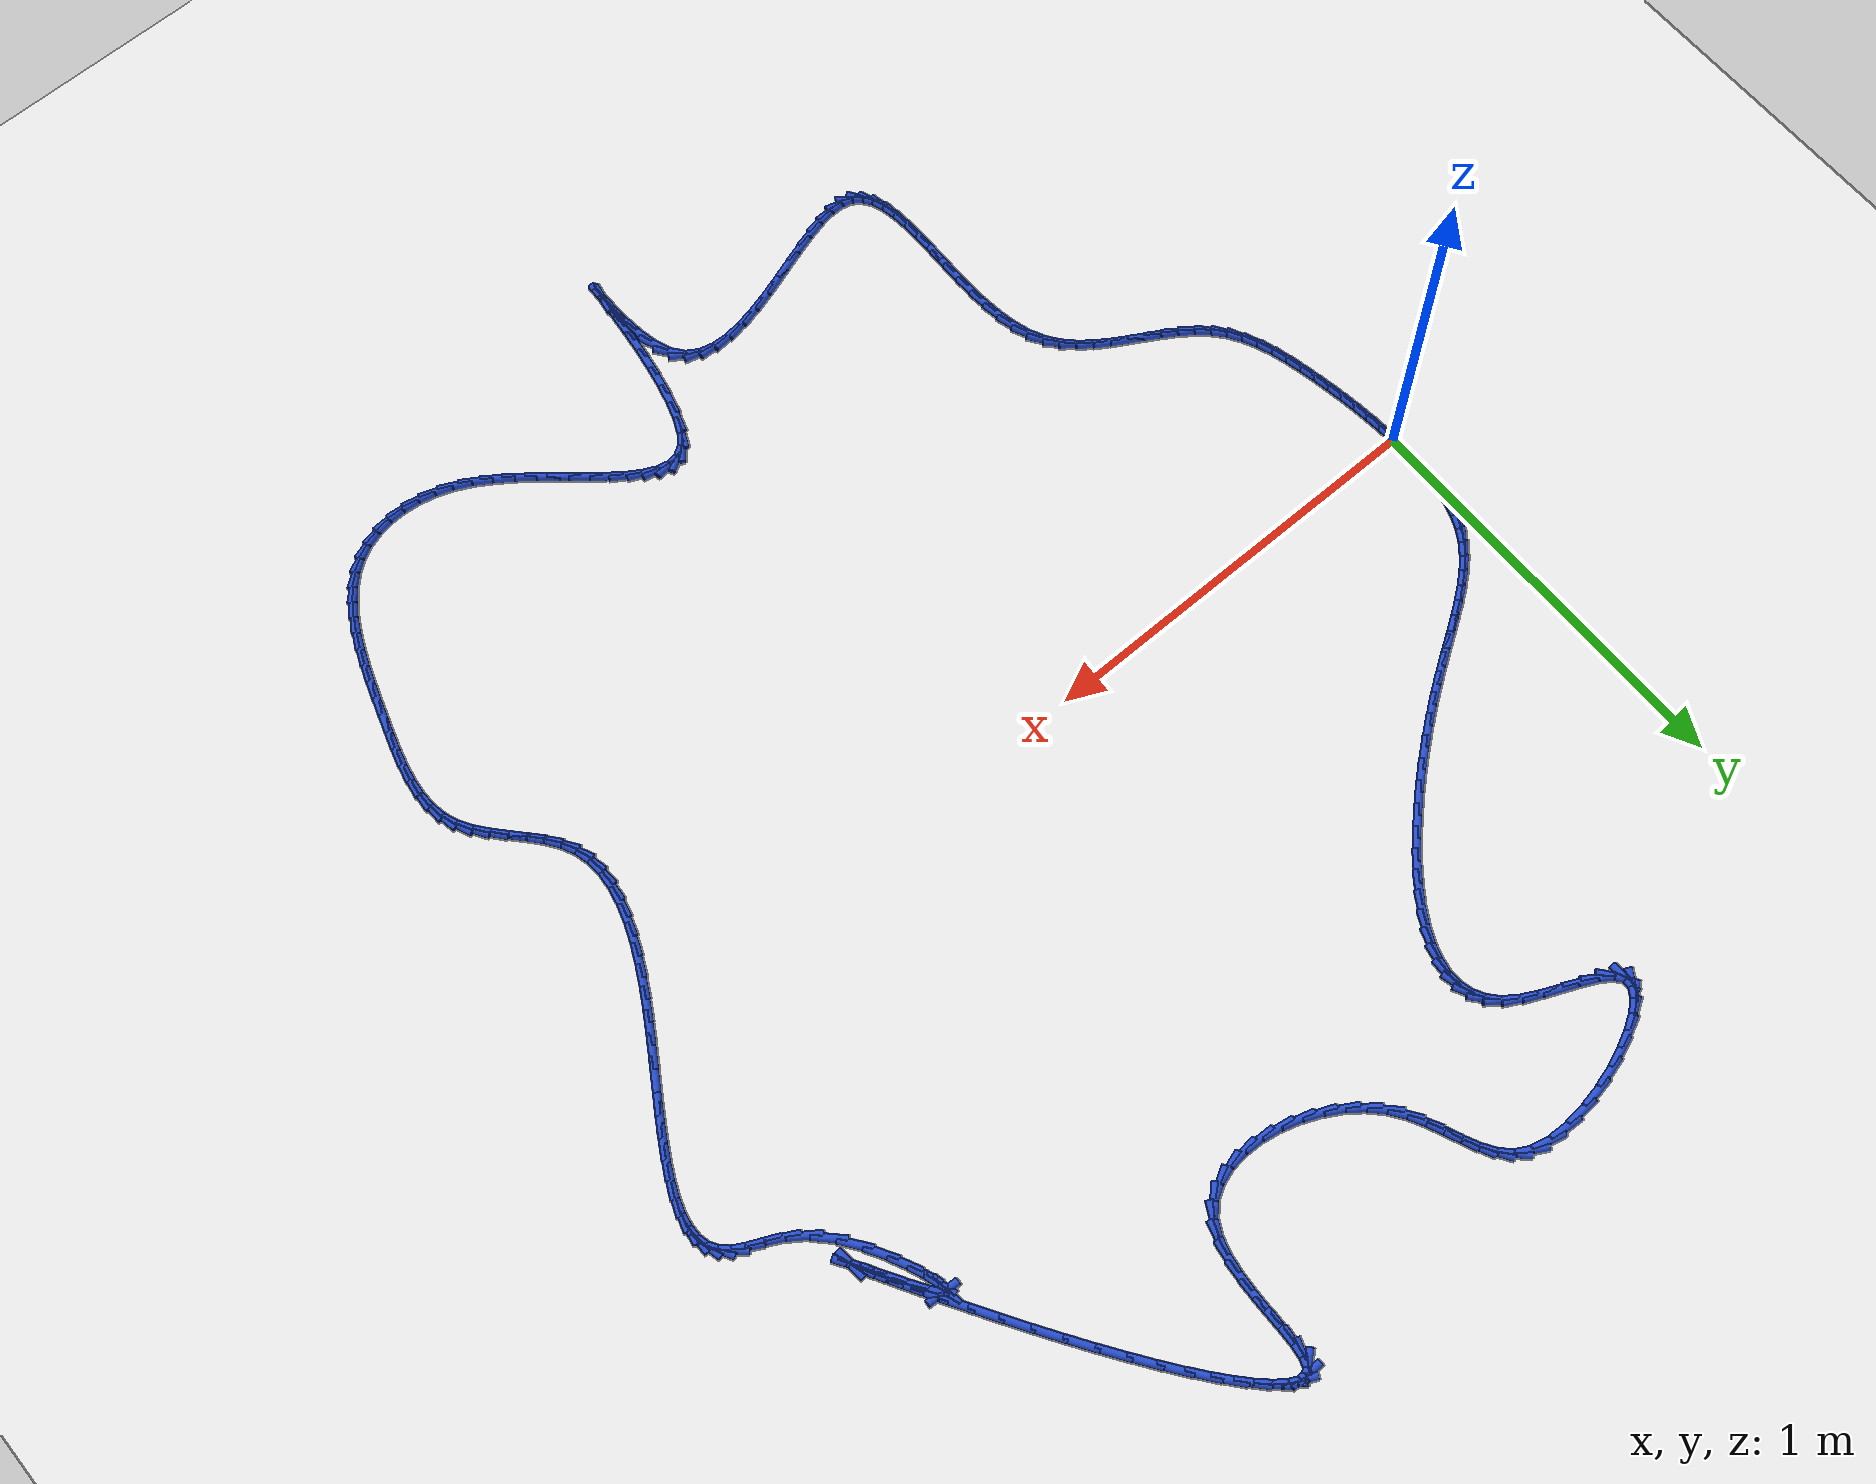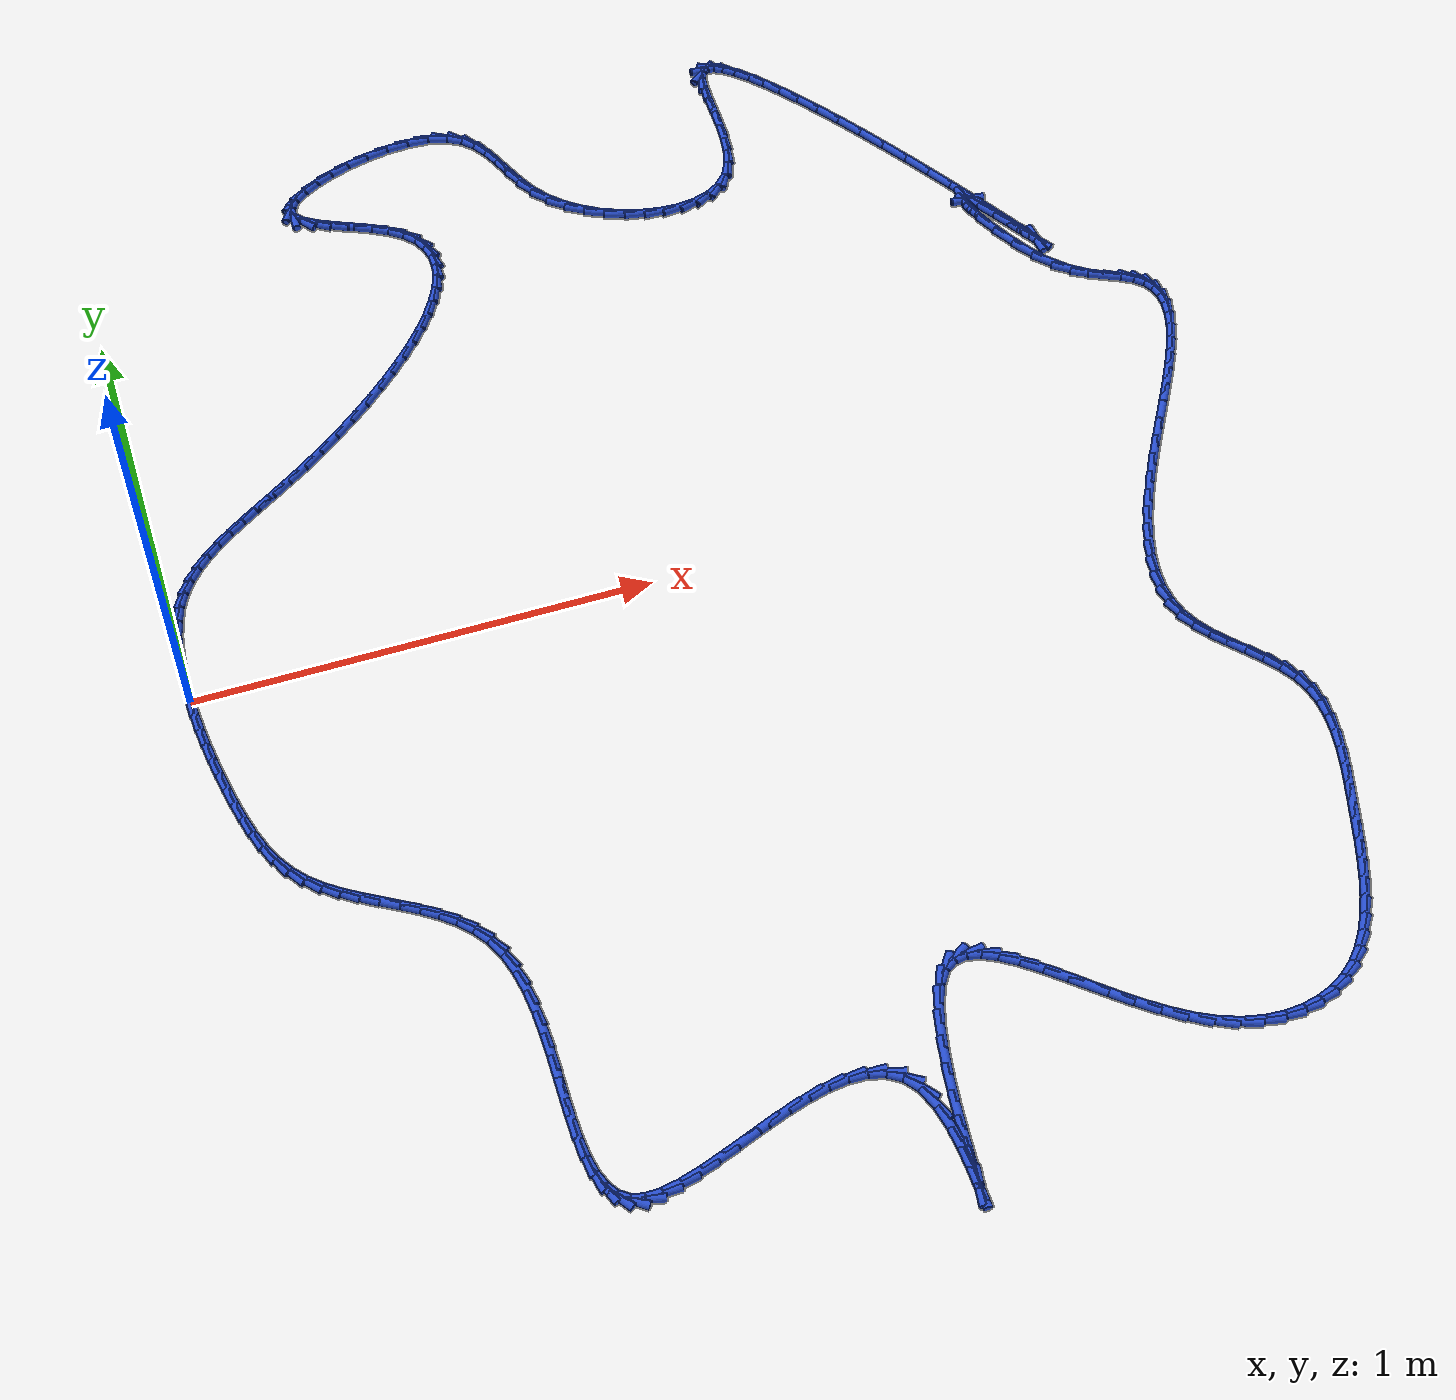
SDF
<sdf version="1.6">
 <world name="default">
  <light name="sun" type="directional">
   <pose>0 0 10 0 -0 0</pose>
   <diffuse>0.8 0.8 0.8 1</diffuse>
   <specular>0.2 0.2 0.2 1</specular>
   <attenuation>
    <range>1000</range>
    <constant>0.9</constant>
    <linear>0.01</linear>
    <quadratic>0.001</quadratic>
   </attenuation>
   <direction>-0.5 0.1 -0.9</direction>
  </light>
  <model name="ground_plane">
   <static>1</static>
   <link name="link">
    <collision name="collision">
     <geometry><plane><normal>0 0 1</normal><size>100 100</size></plane></geometry>
     <surface><friction><ode><mu>100</mu><mu2>50</mu2></ode></friction></surface>
    </collision>
    <visual name="visual">
     <cast_shadows>0</cast_shadows>
     <geometry><plane><normal>0 0 1</normal><size>100 100</size></plane></geometry>
     <material>
      <script><uri>file://media/materials/scripts/gazebo.material</uri><name>Gazebo/WhiteGlow</name></script>
     </material>
    </visual>
   </link>
  </model>
  <gravity>0 0 -9.8</gravity>
  <magnetic_field>6e-06 2.3e-05 -4.2e-05</magnetic_field>
  <atmosphere type="adiabatic"/>
  <physics name="default_physics" default="0" type="ode">
   <max_step_size>0.001</max_step_size>
   <real_time_factor>1</real_time_factor>
   <real_time_update_rate>1000</real_time_update_rate>
  </physics>
  <scene><ambient>0.4 0.4 0.4 1</ambient><background>0.7 0.7 0.7 1</background><shadows>1</shadows></scene>
  <spherical_coordinates>
   <surface_model>EARTH_WGS84</surface_model>
   <latitude_deg>0</latitude_deg>
   <longitude_deg>0</longitude_deg>
   <elevation>0</elevation>
   <heading_deg>0</heading_deg>
  </spherical_coordinates>
  <model name="line">
   <link name="link_0">
    <pose>4.9873299934333204e-18 -6.938893903907228e-18 0.01 0 1.57 -1.5480635645796514</pose>
    <collision name="collision">
     <geometry><cylinder><radius>0.01</radius><length>0.08</length></cylinder></geometry>
    </collision>
    <visual name="visual">
     <material>
      <script><name>Gazebo/Blue</name><uri>file://media/materials/scripts/gazebo.material</uri></script>
     </material>
     <geometry><cylinder><radius>0.01</radius><length>0.08</length></cylinder></geometry>
    </visual>
   </link>
   <link name="link_1">
    <pose>-0.0009229600363917752 0.04059344102352836 0.01 0 1.57 1.5548282706293612</pose>
    <collision name="collision">
     <geometry><cylinder><radius>0.01</radius><length>0.08</length></cylinder></geometry>
    </collision>
    <visual name="visual">
     <material>
      <script><name>Gazebo/Blue</name><uri>file://media/materials/scripts/gazebo.material</uri></script>
     </material>
     <geometry><cylinder><radius>0.01</radius><length>0.08</length></cylinder></geometry>
    </visual>
   </link>
   <link name="link_2">
    <pose>-0.0002700726943167808 0.08147705538145811 0.01 0 1.57 1.5049284805671514</pose>
    <collision name="collision">
     <geometry><cylinder><radius>0.01</radius><length>0.08</length></cylinder></geometry>
    </collision>
    <visual name="visual">
     <material>
      <script><name>Gazebo/Blue</name><uri>file://media/materials/scripts/gazebo.material</uri></script>
     </material>
     <geometry><cylinder><radius>0.01</radius><length>0.08</length></cylinder></geometry>
    </visual>
   </link>
   <link name="link_3">
    <pose>0.0024001554686594066 0.1219575862958889 0.01 0 1.57 1.4412936719225298</pose>
    <collision name="collision">
     <geometry><cylinder><radius>0.01</radius><length>0.08</length></cylinder></geometry>
    </collision>
    <visual name="visual">
     <material>
      <script><name>Gazebo/Blue</name><uri>file://media/materials/scripts/gazebo.material</uri></script>
     </material>
     <geometry><cylinder><radius>0.01</radius><length>0.08</length></cylinder></geometry>
    </visual>
   </link>
   <link name="link_4">
    <pose>0.0075292178949712026 0.1613417769889203 0.01 0 1.57 1.360379430221691</pose>
    <collision name="collision">
     <geometry><cylinder><radius>0.01</radius><length>0.08</length></cylinder></geometry>
    </collision>
    <visual name="visual">
     <material>
      <script><name>Gazebo/Blue</name><uri>file://media/materials/scripts/gazebo.material</uri></script>
     </material>
     <geometry><cylinder><radius>0.01</radius><length>0.08</length></cylinder></geometry>
    </visual>
   </link>
   <link name="link_5">
    <pose>0.015558608027053025 0.1989363706826521 0.01 0 1.57 1.2575978438960318</pose>
    <collision name="collision">
     <geometry><cylinder><radius>0.01</radius><length>0.08</length></cylinder></geometry>
    </collision>
    <visual name="visual">
     <material>
      <script><name>Gazebo/Blue</name><uri>file://media/materials/scripts/gazebo.material</uri></script>
     </material>
     <geometry><cylinder><radius>0.01</radius><length>0.08</length></cylinder></geometry>
    </visual>
   </link>
   <link name="link_6">
    <pose>0.026929819307339294 0.23404811059918393 0.01 0 1.57 1.13094103516065</pose>
    <collision name="collision">
     <geometry><cylinder><radius>0.01</radius><length>0.08</length></cylinder></geometry>
    </collision>
    <visual name="visual">
     <material>
      <script><name>Gazebo/Blue</name><uri>file://media/materials/scripts/gazebo.material</uri></script>
     </material>
     <geometry><cylinder><radius>0.01</radius><length>0.08</length></cylinder></geometry>
    </visual>
   </link>
   <link name="link_7">
    <pose>0.042015793141415195 0.2661047475424821 0.01 0 1.57 1.0006326228099576</pose>
    <collision name="collision">
     <geometry><cylinder><radius>0.01</radius><length>0.08</length></cylinder></geometry>
    </collision>
    <visual name="visual">
     <material>
      <script><name>Gazebo/Blue</name><uri>file://media/materials/scripts/gazebo.material</uri></script>
     </material>
     <geometry><cylinder><radius>0.01</radius><length>0.08</length></cylinder></geometry>
    </visual>
   </link>
   <link name="link_8">
    <pose>0.06074627015875192 0.29531636726473653 0.01 0 1.57 0.8821932592368898</pose>
    <collision name="collision">
     <geometry><cylinder><radius>0.01</radius><length>0.08</length></cylinder></geometry>
    </collision>
    <visual name="visual">
     <material>
      <script><name>Gazebo/Blue</name><uri>file://media/materials/scripts/gazebo.material</uri></script>
     </material>
     <geometry><cylinder><radius>0.01</radius><length>0.08</length></cylinder></geometry>
    </visual>
   </link>
   <link name="link_9">
    <pose>0.082874712873556 0.3222042204294159 0.01 0 1.57 0.7815604918993285</pose>
    <collision name="collision">
     <geometry><cylinder><radius>0.01</radius><length>0.08</length></cylinder></geometry>
    </collision>
    <visual name="visual">
     <material>
      <script><name>Gazebo/Blue</name><uri>file://media/materials/scripts/gazebo.material</uri></script>
     </material>
     <geometry><cylinder><radius>0.01</radius><length>0.08</length></cylinder></geometry>
    </visual>
   </link>
   <link name="link_10">
    <pose>0.10815413310473726 0.3472903532642135 0.01 0 1.57 0.7014076883443885</pose>
    <collision name="collision">
     <geometry><cylinder><radius>0.01</radius><length>0.08</length></cylinder></geometry>
    </collision>
    <visual name="visual">
     <material>
      <script><name>Gazebo/Blue</name><uri>file://media/materials/scripts/gazebo.material</uri></script>
     </material>
     <geometry><cylinder><radius>0.01</radius><length>0.08</length></cylinder></geometry>
    </visual>
   </link>
   <link name="link_11">
    <pose>0.13633754267120546 0.37109681199682254 0.01 0 1.57 0.6418081495975494</pose>
    <collision name="collision">
     <geometry><cylinder><radius>0.01</radius><length>0.08</length></cylinder></geometry>
    </collision>
    <visual name="visual">
     <material>
      <script><name>Gazebo/Blue</name><uri>file://media/materials/scripts/gazebo.material</uri></script>
     </material>
     <geometry><cylinder><radius>0.01</radius><length>0.08</length></cylinder></geometry>
    </visual>
   </link>
   <link name="link_12">
    <pose>0.16717795339187047 0.3941456428549365 0.01 0 1.57 0.6013387917738968</pose>
    <collision name="collision">
     <geometry><cylinder><radius>0.01</radius><length>0.08</length></cylinder></geometry>
    </collision>
    <visual name="visual">
     <material>
      <script><name>Gazebo/Blue</name><uri>file://media/materials/scripts/gazebo.material</uri></script>
     </material>
     <geometry><cylinder><radius>0.01</radius><length>0.08</length></cylinder></geometry>
    </visual>
   </link>
   <link name="link_13">
    <pose>0.20042837708564198 0.4169588920662482 0.01 0 1.57 0.5779809115850214</pose>
    <collision name="collision">
     <geometry><cylinder><radius>0.01</radius><length>0.08</length></cylinder></geometry>
    </collision>
    <visual name="visual">
     <material>
      <script><name>Gazebo/Blue</name><uri>file://media/materials/scripts/gazebo.material</uri></script>
     </material>
     <geometry><cylinder><radius>0.01</radius><length>0.08</length></cylinder></geometry>
    </visual>
   </link>
   <link name="link_14">
    <pose>0.23584182557142985 0.4400586058584511 0.01 0 1.57 0.5696429249281969</pose>
    <collision name="collision">
     <geometry><cylinder><radius>0.01</radius><length>0.08</length></cylinder></geometry>
    </collision>
    <visual name="visual">
     <material>
      <script><name>Gazebo/Blue</name><uri>file://media/materials/scripts/gazebo.material</uri></script>
     </material>
     <geometry><cylinder><radius>0.01</radius><length>0.08</length></cylinder></geometry>
    </visual>
   </link>
   <link name="link_15">
    <pose>0.27317131066814393 0.4639668304592385 0.01 0 1.57 0.5743850118716567</pose>
    <collision name="collision">
     <geometry><cylinder><radius>0.01</radius><length>0.08</length></cylinder></geometry>
    </collision>
    <visual name="visual">
     <material>
      <script><name>Gazebo/Blue</name><uri>file://media/materials/scripts/gazebo.material</uri></script>
     </material>
     <geometry><cylinder><radius>0.01</radius><length>0.08</length></cylinder></geometry>
    </visual>
   </link>
   <link name="link_16">
    <pose>0.3121698441946939 0.4892056120963036 0.01 0 1.57 0.5904657292362538</pose>
    <collision name="collision">
     <geometry><cylinder><radius>0.01</radius><length>0.08</length></cylinder></geometry>
    </collision>
    <visual name="visual">
     <material>
      <script><name>Gazebo/Blue</name><uri>file://media/materials/scripts/gazebo.material</uri></script>
     </material>
     <geometry><cylinder><radius>0.01</radius><length>0.08</length></cylinder></geometry>
    </visual>
   </link>
   <link name="link_17">
    <pose>0.35259029793988755 0.516296627927061 0.01 0 1.57 0.6140329280952556</pose>
    <collision name="collision">
     <geometry><cylinder><radius>0.01</radius><length>0.08</length></cylinder></geometry>
    </collision>
    <visual name="visual">
     <material>
      <script><name>Gazebo/Blue</name><uri>file://media/materials/scripts/gazebo.material</uri></script>
     </material>
     <geometry><cylinder><radius>0.01</radius><length>0.08</length></cylinder></geometry>
    </visual>
   </link>
   <link name="link_18">
    <pose>0.39411156914956247 0.5455665841362922 0.01 0 1.57 0.6386442907082173</pose>
    <collision name="collision">
     <geometry><cylinder><radius>0.01</radius><length>0.08</length></cylinder></geometry>
    </collision>
    <visual name="visual">
     <material>
      <script><name>Gazebo/Blue</name><uri>file://media/materials/scripts/gazebo.material</uri></script>
     </material>
     <geometry><cylinder><radius>0.01</radius><length>0.08</length></cylinder></geometry>
    </visual>
   </link>
   <link name="link_19">
    <pose>0.43621727119226417 0.5768274870408742 0.01 0 1.57 0.6640357894327094</pose>
    <collision name="collision">
     <geometry><cylinder><radius>0.01</radius><length>0.08</length></cylinder></geometry>
    </collision>
    <visual name="visual">
     <material>
      <script><name>Gazebo/Blue</name><uri>file://media/materials/scripts/gazebo.material</uri></script>
     </material>
     <geometry><cylinder><radius>0.01</radius><length>0.08</length></cylinder></geometry>
    </visual>
   </link>
   <link name="link_20">
    <pose>0.4783591669392957 0.6098073962082097 0.01 0 1.57 0.6909758881749642</pose>
    <collision name="collision">
     <geometry><cylinder><radius>0.01</radius><length>0.08</length></cylinder></geometry>
    </collision>
    <visual name="visual">
     <material>
      <script><name>Gazebo/Blue</name><uri>file://media/materials/scripts/gazebo.material</uri></script>
     </material>
     <geometry><cylinder><radius>0.01</radius><length>0.08</length></cylinder></geometry>
    </visual>
   </link>
   <link name="link_21">
    <pose>0.5199890192619602 0.6442343712057014 0.01 0 1.57 0.7202762208391208</pose>
    <collision name="collision">
     <geometry><cylinder><radius>0.01</radius><length>0.08</length></cylinder></geometry>
    </collision>
    <visual name="visual">
     <material>
      <script><name>Gazebo/Blue</name><uri>file://media/materials/scripts/gazebo.material</uri></script>
     </material>
     <geometry><cylinder><radius>0.01</radius><length>0.08</length></cylinder></geometry>
    </visual>
   </link>
   <link name="link_22">
    <pose>0.5605585910315608 0.6798364716007519 0.01 0 1.57 0.7528683962873446</pose>
    <collision name="collision">
     <geometry><cylinder><radius>0.01</radius><length>0.08</length></cylinder></geometry>
    </collision>
    <visual name="visual">
     <material>
      <script><name>Gazebo/Blue</name><uri>file://media/materials/scripts/gazebo.material</uri></script>
     </material>
     <geometry><cylinder><radius>0.01</radius><length>0.08</length></cylinder></geometry>
    </visual>
   </link>
   <link name="link_23">
    <pose>0.5995196451194006 0.7163417569607639 0.01 0 1.57 0.7898913288511158</pose>
    <collision name="collision">
     <geometry><cylinder><radius>0.01</radius><length>0.08</length></cylinder></geometry>
    </collision>
    <visual name="visual">
     <material>
      <script><name>Gazebo/Blue</name><uri>file://media/materials/scripts/gazebo.material</uri></script>
     </material>
     <geometry><cylinder><radius>0.01</radius><length>0.08</length></cylinder></geometry>
    </visual>
   </link>
   <link name="link_24">
    <pose>0.6363239443967829 0.7534782868531401 0.01 0 1.57 0.8328033633133962</pose>
    <collision name="collision">
     <geometry><cylinder><radius>0.01</radius><length>0.08</length></cylinder></geometry>
    </collision>
    <visual name="visual">
     <material>
      <script><name>Gazebo/Blue</name><uri>file://media/materials/scripts/gazebo.material</uri></script>
     </material>
     <geometry><cylinder><radius>0.01</radius><length>0.08</length></cylinder></geometry>
    </visual>
   </link>
   <link name="link_25">
    <pose>0.6704232517350104 0.7909741208452833 0.01 0 1.57 0.8835356502385009</pose>
    <collision name="collision">
     <geometry><cylinder><radius>0.01</radius><length>0.08</length></cylinder></geometry>
    </collision>
    <visual name="visual">
     <material>
      <script><name>Gazebo/Blue</name><uri>file://media/materials/scripts/gazebo.material</uri></script>
     </material>
     <geometry><cylinder><radius>0.01</radius><length>0.08</length></cylinder></geometry>
    </visual>
   </link>
   <link name="link_26">
    <pose>0.7012693300053867 0.8285573185045962 0.01 0 1.57 0.9447053411816257</pose>
    <collision name="collision">
     <geometry><cylinder><radius>0.01</radius><length>0.08</length></cylinder></geometry>
    </collision>
    <visual name="visual">
     <material>
      <script><name>Gazebo/Blue</name><uri>file://media/materials/scripts/gazebo.material</uri></script>
     </material>
     <geometry><cylinder><radius>0.01</radius><length>0.08</length></cylinder></geometry>
    </visual>
   </link>
   <link name="link_27">
    <pose>0.728313942079215 0.8659559393984819 0.01 0 1.57 1.0199014087999074</pose>
    <collision name="collision">
     <geometry><cylinder><radius>0.01</radius><length>0.08</length></cylinder></geometry>
    </collision>
    <visual name="visual">
     <material>
      <script><name>Gazebo/Blue</name><uri>file://media/materials/scripts/gazebo.material</uri></script>
     </material>
     <geometry><cylinder><radius>0.01</radius><length>0.08</length></cylinder></geometry>
    </visual>
   </link>
   <link name="link_28">
    <pose>0.7510088508277979 0.9028980430943424 0.01 0 1.57 1.1140171557062835</pose>
    <collision name="collision">
     <geometry><cylinder><radius>0.01</radius><length>0.08</length></cylinder></geometry>
    </collision>
    <visual name="visual">
     <material>
      <script><name>Gazebo/Blue</name><uri>file://media/materials/scripts/gazebo.material</uri></script>
     </material>
     <geometry><cylinder><radius>0.01</radius><length>0.08</length></cylinder></geometry>
    </visual>
   </link>
   <link name="link_29">
    <pose>0.7688058191224388 0.9391116891595807 0.01 0 1.57 1.2334599864878217</pose>
    <collision name="collision">
     <geometry><cylinder><radius>0.01</radius><length>0.08</length></cylinder></geometry>
    </collision>
    <visual name="visual">
     <material>
      <script><name>Gazebo/Blue</name><uri>file://media/materials/scripts/gazebo.material</uri></script>
     </material>
     <geometry><cylinder><radius>0.01</radius><length>0.08</length></cylinder></geometry>
    </visual>
   </link>
   <link name="link_30">
    <pose>0.7811566098344409 0.9743249371615997 0.01 0 1.57 1.38566312047637</pose>
    <collision name="collision">
     <geometry><cylinder><radius>0.01</radius><length>0.08</length></cylinder></geometry>
    </collision>
    <visual name="visual">
     <material>
      <script><name>Gazebo/Blue</name><uri>file://media/materials/scripts/gazebo.material</uri></script>
     </material>
     <geometry><cylinder><radius>0.01</radius><length>0.08</length></cylinder></geometry>
    </visual>
   </link>
   <link name="link_31">
    <pose>0.7875129858351073 1.0082658466678018 0.01 0 1.57 -1.565046537904039</pose>
    <collision name="collision">
     <geometry><cylinder><radius>0.01</radius><length>0.08</length></cylinder></geometry>
    </collision>
    <visual name="visual">
     <material>
      <script><name>Gazebo/Blue</name><uri>file://media/materials/scripts/gazebo.material</uri></script>
     </material>
     <geometry><cylinder><radius>0.01</radius><length>0.08</length></cylinder></geometry>
    </visual>
   </link>
   <link name="link_32">
    <pose>0.7873267099957412 1.0406624772455901 0.01 0 1.57 -1.3371733908192796</pose>
    <collision name="collision">
     <geometry><cylinder><radius>0.01</radius><length>0.08</length></cylinder></geometry>
    </collision>
    <visual name="visual">
     <material>
      <script><name>Gazebo/Blue</name><uri>file://media/materials/scripts/gazebo.material</uri></script>
     </material>
     <geometry><cylinder><radius>0.01</radius><length>0.08</length></cylinder></geometry>
    </visual>
   </link>
   <link name="link_33">
    <pose>0.7800495451876455 1.0712428884623666 0.01 0 1.57 -1.0885094915099842</pose>
    <collision name="collision">
     <geometry><cylinder><radius>0.01</radius><length>0.08</length></cylinder></geometry>
    </collision>
    <visual name="visual">
     <material>
      <script><name>Gazebo/Blue</name><uri>file://media/materials/scripts/gazebo.material</uri></script>
     </material>
     <geometry><cylinder><radius>0.01</radius><length>0.08</length></cylinder></geometry>
    </visual>
   </link>
   <link name="link_34">
    <pose>0.7651332542821235 1.099735139885535 0.01 0 1.57 -0.8468308192867534</pose>
    <collision name="collision">
     <geometry><cylinder><radius>0.01</radius><length>0.08</length></cylinder></geometry>
    </collision>
    <visual name="visual">
     <material>
      <script><name>Gazebo/Blue</name><uri>file://media/materials/scripts/gazebo.material</uri></script>
     </material>
     <geometry><cylinder><radius>0.01</radius><length>0.08</length></cylinder></geometry>
    </visual>
   </link>
   <link name="link_35">
    <pose>0.7420296001504784 1.1258672910824978 0.01 0 1.57 -0.6370304192301732</pose>
    <collision name="collision">
     <geometry><cylinder><radius>0.01</radius><length>0.08</length></cylinder></geometry>
    </collision>
    <visual name="visual">
     <material>
      <script><name>Gazebo/Blue</name><uri>file://media/materials/scripts/gazebo.material</uri></script>
     </material>
     <geometry><cylinder><radius>0.01</radius><length>0.08</length></cylinder></geometry>
    </visual>
   </link>
   <link name="link_36">
    <pose>0.7102517503253716 1.1493809372589332 0.01 0 1.57 -0.4959302152229993</pose>
    <collision name="collision">
     <geometry><cylinder><radius>0.01</radius><length>0.08</length></cylinder></geometry>
    </collision>
    <visual name="visual">
     <material>
      <script><name>Gazebo/Blue</name><uri>file://media/materials/scripts/gazebo.material</uri></script>
     </material>
     <geometry><cylinder><radius>0.01</radius><length>0.08</length></cylinder></geometry>
    </visual>
   </link>
   <link name="link_37">
    <pose>0.6712990695357276 1.1704554978214643 0.01 0 1.57 -0.42915011345294274</pose>
    <collision name="collision">
     <geometry><cylinder><radius>0.01</radius><length>0.08</length></cylinder></geometry>
    </collision>
    <visual name="visual">
     <material>
      <script><name>Gazebo/Blue</name><uri>file://media/materials/scripts/gazebo.material</uri></script>
     </material>
     <geometry><cylinder><radius>0.01</radius><length>0.08</length></cylinder></geometry>
    </visual>
   </link>
   <link name="link_38">
    <pose>0.629040482086128 1.189792722250363 0.01 0 1.57 -0.41545951307137086</pose>
    <collision name="collision">
     <geometry><cylinder><radius>0.01</radius><length>0.08</length></cylinder></geometry>
    </collision>
    <visual name="visual">
     <material>
      <script><name>Gazebo/Blue</name><uri>file://media/materials/scripts/gazebo.material</uri></script>
     </material>
     <geometry><cylinder><radius>0.01</radius><length>0.08</length></cylinder></geometry>
    </visual>
   </link>
   <link name="link_39">
    <pose>0.5874837387922698 1.2081249620257482 0.01 0 1.57 -0.4557142152066989</pose>
    <collision name="collision">
     <geometry><cylinder><radius>0.01</radius><length>0.08</length></cylinder></geometry>
    </collision>
    <visual name="visual">
     <material>
      <script><name>Gazebo/Blue</name><uri>file://media/materials/scripts/gazebo.material</uri></script>
     </material>
     <geometry><cylinder><radius>0.01</radius><length>0.08</length></cylinder></geometry>
    </visual>
   </link>
   <link name="link_40">
    <pose>0.5506365904698498 1.2261845686277382 0.01 0 1.57 -0.582224511144512</pose>
    <collision name="collision">
     <geometry><cylinder><radius>0.01</radius><length>0.08</length></cylinder></geometry>
    </collision>
    <visual name="visual">
     <material>
      <script><name>Gazebo/Blue</name><uri>file://media/materials/scripts/gazebo.material</uri></script>
     </material>
     <geometry><cylinder><radius>0.01</radius><length>0.08</length></cylinder></geometry>
    </visual>
   </link>
   <link name="link_41">
    <pose>0.5225067879345647 1.2447038935364532 0.01 0 1.57 -0.9074292882225848</pose>
    <collision name="collision">
     <geometry><cylinder><radius>0.01</radius><length>0.08</length></cylinder></geometry>
    </collision>
    <visual name="visual">
     <material>
      <script><name>Gazebo/Blue</name><uri>file://media/materials/scripts/gazebo.material</uri></script>
     </material>
     <geometry><cylinder><radius>0.01</radius><length>0.08</length></cylinder></geometry>
    </visual>
   </link>
   <link name="link_42">
    <pose>0.5071020579172593 1.2644152819043875 0.01 0 1.57 1.5619311502329325</pose>
    <collision name="collision">
     <geometry><cylinder><radius>0.01</radius><length>0.08</length></cylinder></geometry>
    </collision>
    <visual name="visual">
     <material>
      <script><name>Gazebo/Blue</name><uri>file://media/materials/scripts/gazebo.material</uri></script>
     </material>
     <geometry><cylinder><radius>0.01</radius><length>0.08</length></cylinder></geometry>
    </visual>
   </link>
   <link name="link_43">
    <pose>0.5072912154181342 1.285751861513983 0.01 0 1.57 0.9951732054812551</pose>
    <collision name="collision">
     <geometry><cylinder><radius>0.01</radius><length>0.08</length></cylinder></geometry>
    </collision>
    <visual name="visual">
     <material>
      <script><name>Gazebo/Blue</name><uri>file://media/materials/scripts/gazebo.material</uri></script>
     </material>
     <geometry><cylinder><radius>0.01</radius><length>0.08</length></cylinder></geometry>
    </visual>
   </link>
   <link name="link_44">
    <pose>0.521759657993905 1.3080476836068136 0.01 0 1.57 0.7008625635395084</pose>
    <collision name="collision">
     <geometry><cylinder><radius>0.01</radius><length>0.08</length></cylinder></geometry>
    </collision>
    <visual name="visual">
     <material>
      <script><name>Gazebo/Blue</name><uri>file://media/materials/scripts/gazebo.material</uri></script>
     </material>
     <geometry><cylinder><radius>0.01</radius><length>0.08</length></cylinder></geometry>
    </visual>
   </link>
   <link name="link_45">
    <pose>0.5482324966794412 1.3303845108582433 0.01 0 1.57 0.5350849434351569</pose>
    <collision name="collision">
     <geometry><cylinder><radius>0.01</radius><length>0.08</length></cylinder></geometry>
    </collision>
    <visual name="visual">
     <material>
      <script><name>Gazebo/Blue</name><uri>file://media/materials/scripts/gazebo.material</uri></script>
     </material>
     <geometry><cylinder><radius>0.01</radius><length>0.08</length></cylinder></geometry>
    </visual>
   </link>
   <link name="link_46">
    <pose>0.5844348425096134 1.3518441059436375 0.01 0 1.57 0.4232061116509862</pose>
    <collision name="collision">
     <geometry><cylinder><radius>0.01</radius><length>0.08</length></cylinder></geometry>
    </collision>
    <visual name="visual">
     <material>
      <script><name>Gazebo/Blue</name><uri>file://media/materials/scripts/gazebo.material</uri></script>
     </material>
     <geometry><cylinder><radius>0.01</radius><length>0.08</length></cylinder></geometry>
    </visual>
   </link>
   <link name="link_47">
    <pose>0.6280918065192911 1.3715082315383598 0.01 0 1.57 0.33407439497958863</pose>
    <collision name="collision">
     <geometry><cylinder><radius>0.01</radius><length>0.08</length></cylinder></geometry>
    </collision>
    <visual name="visual">
     <material>
      <script><name>Gazebo/Blue</name><uri>file://media/materials/scripts/gazebo.material</uri></script>
     </material>
     <geometry><cylinder><radius>0.01</radius><length>0.08</length></cylinder></geometry>
    </visual>
   </link>
   <link name="link_48">
    <pose>0.6769284997433443 1.3884586503177745 0.01 0 1.57 0.25193484757584</pose>
    <collision name="collision">
     <geometry><cylinder><radius>0.01</radius><length>0.08</length></cylinder></geometry>
    </collision>
    <visual name="visual">
     <material>
      <script><name>Gazebo/Blue</name><uri>file://media/materials/scripts/gazebo.material</uri></script>
     </material>
     <geometry><cylinder><radius>0.01</radius><length>0.08</length></cylinder></geometry>
    </visual>
   </link>
   <link name="link_49">
    <pose>0.728670033216643 1.401777124957246 0.01 0 1.57 0.16588637497811437</pose>
    <collision name="collision">
     <geometry><cylinder><radius>0.01</radius><length>0.08</length></cylinder></geometry>
    </collision>
    <visual name="visual">
     <material>
      <script><name>Gazebo/Blue</name><uri>file://media/materials/scripts/gazebo.material</uri></script>
     </material>
     <geometry><cylinder><radius>0.01</radius><length>0.08</length></cylinder></geometry>
    </visual>
   </link>
   <link name="link_50">
    <pose>0.7810415179740574 1.410545418132139 0.01 0 1.57 0.06496068756718525</pose>
    <collision name="collision">
     <geometry><cylinder><radius>0.01</radius><length>0.08</length></cylinder></geometry>
    </collision>
    <visual name="visual">
     <material>
      <script><name>Gazebo/Blue</name><uri>file://media/materials/scripts/gazebo.material</uri></script>
     </material>
     <geometry><cylinder><radius>0.01</radius><length>0.08</length></cylinder></geometry>
    </visual>
   </link>
   <link name="link_51">
    <pose>0.8317680650504571 1.4138452925178175 0.01 0 1.57 -0.06585205017736295</pose>
    <collision name="collision">
     <geometry><cylinder><radius>0.01</radius><length>0.08</length></cylinder></geometry>
    </collision>
    <visual name="visual">
     <material>
      <script><name>Gazebo/Blue</name><uri>file://media/materials/scripts/gazebo.material</uri></script>
     </material>
     <geometry><cylinder><radius>0.01</radius><length>0.08</length></cylinder></geometry>
    </visual>
   </link>
   <link name="link_52">
    <pose>0.878574785480712 1.4107585107896463 0.01 0 1.57 -0.25050219834039555</pose>
    <collision name="collision">
     <geometry><cylinder><radius>0.01</radius><length>0.08</length></cylinder></geometry>
    </collision>
    <visual name="visual">
     <material>
      <script><name>Gazebo/Blue</name><uri>file://media/materials/scripts/gazebo.material</uri></script>
     </material>
     <geometry><cylinder><radius>0.01</radius><length>0.08</length></cylinder></geometry>
    </visual>
   </link>
   <link name="link_53">
    <pose>0.919186790299692 1.4003668356229892 0.01 0 1.57 -0.5156828926272555</pose>
    <collision name="collision">
     <geometry><cylinder><radius>0.01</radius><length>0.08</length></cylinder></geometry>
    </collision>
    <visual name="visual">
     <material>
      <script><name>Gazebo/Blue</name><uri>file://media/materials/scripts/gazebo.material</uri></script>
     </material>
     <geometry><cylinder><radius>0.01</radius><length>0.08</length></cylinder></geometry>
    </visual>
   </link>
   <link name="link_54">
    <pose>0.9516770507973036 1.3819499407858444 0.01 0 1.57 -0.7939372054560259</pose>
    <collision name="collision">
     <geometry><cylinder><radius>0.01</radius><length>0.08</length></cylinder></geometry>
    </collision>
    <visual name="visual">
     <material>
      <script><name>Gazebo/Blue</name><uri>file://media/materials/scripts/gazebo.material</uri></script>
     </material>
     <geometry><cylinder><radius>0.01</radius><length>0.08</length></cylinder></geometry>
    </visual>
   </link>
   <link name="link_55">
    <pose>0.9768511592827533 1.3563421933572517 0.01 0 1.57 -1.0022200515110102</pose>
    <collision name="collision">
     <geometry><cylinder><radius>0.01</radius><length>0.08</length></cylinder></geometry>
    </collision>
    <visual name="visual">
     <material>
      <script><name>Gazebo/Blue</name><uri>file://media/materials/scripts/gazebo.material</uri></script>
     </material>
     <geometry><cylinder><radius>0.01</radius><length>0.08</length></cylinder></geometry>
    </visual>
   </link>
   <link name="link_56">
    <pose>0.9968057489504735 1.325112483284359 0.01 0 1.57 -1.1254508425453265</pose>
    <collision name="collision">
     <geometry><cylinder><radius>0.01</radius><length>0.08</length></cylinder></geometry>
    </collision>
    <visual name="visual">
     <material>
      <script><name>Gazebo/Blue</name><uri>file://media/materials/scripts/gazebo.material</uri></script>
     </material>
     <geometry><cylinder><radius>0.01</radius><length>0.08</length></cylinder></geometry>
    </visual>
   </link>
   <link name="link_57">
    <pose>1.0136451058212073 1.2898340545018536 0.01 0 1.57 -1.1738041061889504</pose>
    <collision name="collision">
     <geometry><cylinder><radius>0.01</radius><length>0.08</length></cylinder></geometry>
    </collision>
    <visual name="visual">
     <material>
      <script><name>Gazebo/Blue</name><uri>file://media/materials/scripts/gazebo.material</uri></script>
     </material>
     <geometry><cylinder><radius>0.01</radius><length>0.08</length></cylinder></geometry>
    </visual>
   </link>
   <link name="link_58">
    <pose>1.0294735159156985 1.252080150944426 0.01 0 1.57 -1.1581754929664165</pose>
    <collision name="collision">
     <geometry><cylinder><radius>0.01</radius><length>0.08</length></cylinder></geometry>
    </collision>
    <visual name="visual">
     <material>
      <script><name>Gazebo/Blue</name><uri>file://media/materials/scripts/gazebo.material</uri></script>
     </material>
     <geometry><cylinder><radius>0.01</radius><length>0.08</length></cylinder></geometry>
    </visual>
   </link>
   <link name="link_59">
    <pose>1.046395265254691 1.2134240165467645 0.01 0 1.57 -1.083699620009665</pose>
    <collision name="collision">
     <geometry><cylinder><radius>0.01</radius><length>0.08</length></cylinder></geometry>
    </collision>
    <visual name="visual">
     <material>
      <script><name>Gazebo/Blue</name><uri>file://media/materials/scripts/gazebo.material</uri></script>
     </material>
     <geometry><cylinder><radius>0.01</radius><length>0.08</length></cylinder></geometry>
    </visual>
   </link>
   <link name="link_60">
    <pose>1.0665146398589287 1.1754388952435593 0.01 0 1.57 -0.9526578173562713</pose>
    <collision name="collision">
     <geometry><cylinder><radius>0.01</radius><length>0.08</length></cylinder></geometry>
    </collision>
    <visual name="visual">
     <material>
      <script><name>Gazebo/Blue</name><uri>file://media/materials/scripts/gazebo.material</uri></script>
     </material>
     <geometry><cylinder><radius>0.01</radius><length>0.08</length></cylinder></geometry>
    </visual>
   </link>
   <link name="link_61">
    <pose>1.0919311831659992 1.1396964485971963 0.01 0 1.57 -0.7918750370406433</pose>
    <collision name="collision">
     <geometry><cylinder><radius>0.01</radius><length>0.08</length></cylinder></geometry>
    </collision>
    <visual name="visual">
     <material>
      <script><name>Gazebo/Blue</name><uri>file://media/materials/scripts/gazebo.material</uri></script>
     </material>
     <geometry><cylinder><radius>0.01</radius><length>0.08</length></cylinder></geometry>
    </visual>
   </link>
   <link name="link_62">
    <pose>1.1237694731234942 1.10744303899532 0.01 0 1.57 -0.6489936199285218</pose>
    <collision name="collision">
     <geometry><cylinder><radius>0.01</radius><length>0.08</length></cylinder></geometry>
    </collision>
    <visual name="visual">
     <material>
      <script><name>Gazebo/Blue</name><uri>file://media/materials/scripts/gazebo.material</uri></script>
     </material>
     <geometry><cylinder><radius>0.01</radius><length>0.08</length></cylinder></geometry>
    </visual>
   </link>
   <link name="link_63">
    <pose>1.1609935836100305 1.0792041723461596 0.01 0 1.57 -0.5228771626686369</pose>
    <collision name="collision">
     <geometry><cylinder><radius>0.01</radius><length>0.08</length></cylinder></geometry>
    </collision>
    <visual name="visual">
     <material>
      <script><name>Gazebo/Blue</name><uri>file://media/materials/scripts/gazebo.material</uri></script>
     </material>
     <geometry><cylinder><radius>0.01</radius><length>0.08</length></cylinder></geometry>
    </visual>
   </link>
   <link name="link_64">
    <pose>1.2022775340230665 1.0554085773034478 0.01 0 1.57 -0.40602014809166076</pose>
    <collision name="collision">
     <geometry><cylinder><radius>0.01</radius><length>0.08</length></cylinder></geometry>
    </collision>
    <visual name="visual">
     <material>
      <script><name>Gazebo/Blue</name><uri>file://media/materials/scripts/gazebo.material</uri></script>
     </material>
     <geometry><cylinder><radius>0.01</radius><length>0.08</length></cylinder></geometry>
    </visual>
   </link>
   <link name="link_65">
    <pose>1.2462953437600597 1.0364849825209161 0.01 0 1.57 -0.29135902797094676</pose>
    <collision name="collision">
     <geometry><cylinder><radius>0.01</radius><length>0.08</length></cylinder></geometry>
    </collision>
    <visual name="visual">
     <material>
      <script><name>Gazebo/Blue</name><uri>file://media/materials/scripts/gazebo.material</uri></script>
     </material>
     <geometry><cylinder><radius>0.01</radius><length>0.08</length></cylinder></geometry>
    </visual>
   </link>
   <link name="link_66">
    <pose>1.2917210322184682 1.022862116652297 0.01 0 1.57 -0.17174383451556846</pose>
    <collision name="collision">
     <geometry><cylinder><radius>0.01</radius><length>0.08</length></cylinder></geometry>
    </collision>
    <visual name="visual">
     <material>
      <script><name>Gazebo/Blue</name><uri>file://media/materials/scripts/gazebo.material</uri></script>
     </material>
     <geometry><cylinder><radius>0.01</radius><length>0.08</length></cylinder></geometry>
    </visual>
   </link>
   <link name="link_67">
    <pose>1.3372286187957516 1.0149687083513228 0.01 0 1.57 -0.039182031223548366</pose>
    <collision name="collision">
     <geometry><cylinder><radius>0.01</radius><length>0.08</length></cylinder></geometry>
    </collision>
    <visual name="visual">
     <material>
      <script><name>Gazebo/Blue</name><uri>file://media/materials/scripts/gazebo.material</uri></script>
     </material>
     <geometry><cylinder><radius>0.01</radius><length>0.08</length></cylinder></geometry>
    </visual>
   </link>
   <link name="link_68">
    <pose>1.3814921228893657 1.0132334862717256 0.01 0 1.57 0.1158448416204335</pose>
    <collision name="collision">
     <geometry><cylinder><radius>0.01</radius><length>0.08</length></cylinder></geometry>
    </collision>
    <visual name="visual">
     <material>
      <script><name>Gazebo/Blue</name><uri>file://media/materials/scripts/gazebo.material</uri></script>
     </material>
     <geometry><cylinder><radius>0.01</radius><length>0.08</length></cylinder></geometry>
    </visual>
   </link>
   <link name="link_69">
    <pose>1.4231855638967694 1.0180851790672376 0.01 0 1.57 0.30422563138469555</pose>
    <collision name="collision">
     <geometry><cylinder><radius>0.01</radius><length>0.08</length></cylinder></geometry>
    </collision>
    <visual name="visual">
     <material>
      <script><name>Gazebo/Blue</name><uri>file://media/materials/scripts/gazebo.material</uri></script>
     </material>
     <geometry><cylinder><radius>0.01</radius><length>0.08</length></cylinder></geometry>
    </visual>
   </link>
   <link name="link_70">
    <pose>1.4609829612154217 1.0299525153915912 0.01 0 1.57 0.5351318994359345</pose>
    <collision name="collision">
     <geometry><cylinder><radius>0.01</radius><length>0.08</length></cylinder></geometry>
    </collision>
    <visual name="visual">
     <material>
      <script><name>Gazebo/Blue</name><uri>file://media/materials/scripts/gazebo.material</uri></script>
     </material>
     <geometry><cylinder><radius>0.01</radius><length>0.08</length></cylinder></geometry>
    </visual>
   </link>
   <link name="link_71">
    <pose>1.4935583342427794 1.0492642238985181 0.01 0 1.57 0.8071461688032678</pose>
    <collision name="collision">
     <geometry><cylinder><radius>0.01</radius><length>0.08</length></cylinder></geometry>
    </collision>
    <visual name="visual">
     <material>
      <script><name>Gazebo/Blue</name><uri>file://media/materials/scripts/gazebo.material</uri></script>
     </material>
     <geometry><cylinder><radius>0.01</radius><length>0.08</length></cylinder></geometry>
    </visual>
   </link>
   <link name="link_72">
    <pose>1.5195857023763009 1.076449033241751 0.01 0 1.57 1.0832902315650044</pose>
    <collision name="collision">
     <geometry><cylinder><radius>0.01</radius><length>0.08</length></cylinder></geometry>
    </collision>
    <visual name="visual">
     <material>
      <script><name>Gazebo/Blue</name><uri>file://media/materials/scripts/gazebo.material</uri></script>
     </material>
     <geometry><cylinder><radius>0.01</radius><length>0.08</length></cylinder></geometry>
    </visual>
   </link>
   <link name="link_73">
    <pose>1.5381779881284616 1.11151631469418 0.01 0 1.57 1.2844640253839126</pose>
    <collision name="collision">
     <geometry><cylinder><radius>0.01</radius><length>0.08</length></cylinder></geometry>
    </collision>
    <visual name="visual">
     <material>
      <script><name>Gazebo/Blue</name><uri>file://media/materials/scripts/gazebo.material</uri></script>
     </material>
     <geometry><cylinder><radius>0.01</radius><length>0.08</length></cylinder></geometry>
    </visual>
   </link>
   <link name="link_74">
    <pose>1.5503040417743772 1.1527021620582452 0.01 0 1.57 1.4141395153408352</pose>
    <collision name="collision">
     <geometry><cylinder><radius>0.01</radius><length>0.08</length></cylinder></geometry>
    </collision>
    <visual name="visual">
     <material>
      <script><name>Gazebo/Blue</name><uri>file://media/materials/scripts/gazebo.material</uri></script>
     </material>
     <geometry><cylinder><radius>0.01</radius><length>0.08</length></cylinder></geometry>
    </visual>
   </link>
   <link name="link_75">
    <pose>1.557423190929777 1.1977740342921945 0.01 0 1.57 1.494507045484413</pose>
    <collision name="collision">
     <geometry><cylinder><radius>0.01</radius><length>0.08</length></cylinder></geometry>
    </collision>
    <visual name="visual">
     <material>
      <script><name>Gazebo/Blue</name><uri>file://media/materials/scripts/gazebo.material</uri></script>
     </material>
     <geometry><cylinder><radius>0.01</radius><length>0.08</length></cylinder></geometry>
    </visual>
   </link>
   <link name="link_76">
    <pose>1.5609947661585308 1.2444993875374222 0.01 0 1.57 1.5386632714999435</pose>
    <collision name="collision">
     <geometry><cylinder><radius>0.01</radius><length>0.08</length></cylinder></geometry>
    </collision>
    <visual name="visual">
     <material>
      <script><name>Gazebo/Blue</name><uri>file://media/materials/scripts/gazebo.material</uri></script>
     </material>
     <geometry><cylinder><radius>0.01</radius><length>0.08</length></cylinder></geometry>
    </visual>
   </link>
   <link name="link_77">
    <pose>1.56247809802451 1.2906456779353237 0.01 0 1.57 1.5510821324916828</pose>
    <collision name="collision">
     <geometry><cylinder><radius>0.01</radius><length>0.08</length></cylinder></geometry>
    </collision>
    <visual name="visual">
     <material>
      <script><name>Gazebo/Blue</name><uri>file://media/materials/scripts/gazebo.material</uri></script>
     </material>
     <geometry><cylinder><radius>0.01</radius><length>0.08</length></cylinder></geometry>
    </visual>
   </link>
   <link name="link_78">
    <pose>1.5633325170915855 1.3339803616272947 0.01 0 1.57 1.5268232972844278</pose>
    <collision name="collision">
     <geometry><cylinder><radius>0.01</radius><length>0.08</length></cylinder></geometry>
    </collision>
    <visual name="visual">
     <material>
      <script><name>Gazebo/Blue</name><uri>file://media/materials/scripts/gazebo.material</uri></script>
     </material>
     <geometry><cylinder><radius>0.01</radius><length>0.08</length></cylinder></geometry>
    </visual>
   </link>
   <link name="link_79">
    <pose>1.5650173539236287 1.3722708947547293 0.01 0 1.57 1.443335875157329</pose>
    <collision name="collision">
     <geometry><cylinder><radius>0.01</radius><length>0.08</length></cylinder></geometry>
    </collision>
    <visual name="visual">
     <material>
      <script><name>Gazebo/Blue</name><uri>file://media/materials/scripts/gazebo.material</uri></script>
     </material>
     <geometry><cylinder><radius>0.01</radius><length>0.08</length></cylinder></geometry>
    </visual>
   </link>
   <link name="link_80">
    <pose>1.5689919390845097 1.4032847334590235 0.01 0 1.57 1.225981615338795</pose>
    <collision name="collision">
     <geometry><cylinder><radius>0.01</radius><length>0.08</length></cylinder></geometry>
    </collision>
    <visual name="visual">
     <material>
      <script><name>Gazebo/Blue</name><uri>file://media/materials/scripts/gazebo.material</uri></script>
     </material>
     <geometry><cylinder><radius>0.01</radius><length>0.08</length></cylinder></geometry>
    </visual>
   </link>
   <link name="link_81">
    <pose>1.5767156031380996 1.4247893338815723 0.01 0 1.57 0.6809598792912425</pose>
    <collision name="collision">
     <geometry><cylinder><radius>0.01</radius><length>0.08</length></cylinder></geometry>
    </collision>
    <visual name="visual">
     <material>
      <script><name>Gazebo/Blue</name><uri>file://media/materials/scripts/gazebo.material</uri></script>
     </material>
     <geometry><cylinder><radius>0.01</radius><length>0.08</length></cylinder></geometry>
    </visual>
   </link>
   <link name="link_82">
    <pose>1.5893524288314131 1.4350283242391486 0.01 0 1.57 -0.038838497038295984</pose>
    <collision name="collision">
     <geometry><cylinder><radius>0.01</radius><length>0.08</length></cylinder></geometry>
    </collision>
    <visual name="visual">
     <material>
      <script><name>Gazebo/Blue</name><uri>file://media/materials/scripts/gazebo.material</uri></script>
     </material>
     <geometry><cylinder><radius>0.01</radius><length>0.08</length></cylinder></geometry>
    </visual>
   </link>
   <link name="link_83">
    <pose>1.6067603418547112 1.4343518869073464 0.01 0 1.57 -0.4570348716094999</pose>
    <collision name="collision">
     <geometry><cylinder><radius>0.01</radius><length>0.08</length></cylinder></geometry>
    </collision>
    <visual name="visual">
     <material>
      <script><name>Gazebo/Blue</name><uri>file://media/materials/scripts/gazebo.material</uri></script>
     </material>
     <geometry><cylinder><radius>0.01</radius><length>0.08</length></cylinder></geometry>
    </visual>
   </link>
   <link name="link_84">
    <pose>1.6284361903996678 1.423692545644349 0.01 0 1.57 -0.6591435741152268</pose>
    <collision name="collision">
     <geometry><cylinder><radius>0.01</radius><length>0.08</length></cylinder></geometry>
    </collision>
    <visual name="visual">
     <material>
      <script><name>Gazebo/Blue</name><uri>file://media/materials/scripts/gazebo.material</uri></script>
     </material>
     <geometry><cylinder><radius>0.01</radius><length>0.08</length></cylinder></geometry>
    </visual>
   </link>
   <link name="link_85">
    <pose>1.6538768102988748 1.4039828441409143 0.01 0 1.57 -0.7699259685175515</pose>
    <collision name="collision">
     <geometry><cylinder><radius>0.01</radius><length>0.08</length></cylinder></geometry>
    </collision>
    <visual name="visual">
     <material>
      <script><name>Gazebo/Blue</name><uri>file://media/materials/scripts/gazebo.material</uri></script>
     </material>
     <geometry><cylinder><radius>0.01</radius><length>0.08</length></cylinder></geometry>
    </visual>
   </link>
   <link name="link_86">
    <pose>1.6825790373849276 1.376155326087799 0.01 0 1.57 -0.8387840640517336</pose>
    <collision name="collision">
     <geometry><cylinder><radius>0.01</radius><length>0.08</length></cylinder></geometry>
    </collision>
    <visual name="visual">
     <material>
      <script><name>Gazebo/Blue</name><uri>file://media/materials/scripts/gazebo.material</uri></script>
     </material>
     <geometry><cylinder><radius>0.01</radius><length>0.08</length></cylinder></geometry>
    </visual>
   </link>
   <link name="link_87">
    <pose>1.714039707490417 1.3411425351757604 0.01 0 1.57 -0.8857458050305964</pose>
    <collision name="collision">
     <geometry><cylinder><radius>0.01</radius><length>0.08</length></cylinder></geometry>
    </collision>
    <visual name="visual">
     <material>
      <script><name>Gazebo/Blue</name><uri>file://media/materials/scripts/gazebo.material</uri></script>
     </material>
     <geometry><cylinder><radius>0.01</radius><length>0.08</length></cylinder></geometry>
    </visual>
   </link>
   <link name="link_88">
    <pose>1.7477556564479377 1.2998770150955559 0.01 0 1.57 -0.9200702046058342</pose>
    <collision name="collision">
     <geometry><cylinder><radius>0.01</radius><length>0.08</length></cylinder></geometry>
    </collision>
    <visual name="visual">
     <material>
      <script><name>Gazebo/Blue</name><uri>file://media/materials/scripts/gazebo.material</uri></script>
     </material>
     <geometry><cylinder><radius>0.01</radius><length>0.08</length></cylinder></geometry>
    </visual>
   </link>
   <link name="link_89">
    <pose>1.7832237200900827 1.2532913095379417 0.01 0 1.57 -0.9465639448490066</pose>
    <collision name="collision">
     <geometry><cylinder><radius>0.01</radius><length>0.08</length></cylinder></geometry>
    </collision>
    <visual name="visual">
     <material>
      <script><name>Gazebo/Blue</name><uri>file://media/materials/scripts/gazebo.material</uri></script>
     </material>
     <geometry><cylinder><radius>0.01</radius><length>0.08</length></cylinder></geometry>
    </visual>
   </link>
   <link name="link_90">
    <pose>1.8199407342494447 1.2023179621936757 0.01 0 1.57 -0.9679687347214901</pose>
    <collision name="collision">
     <geometry><cylinder><radius>0.01</radius><length>0.08</length></cylinder></geometry>
    </collision>
    <visual name="visual">
     <material>
      <script><name>Gazebo/Blue</name><uri>file://media/materials/scripts/gazebo.material</uri></script>
     </material>
     <geometry><cylinder><radius>0.01</radius><length>0.08</length></cylinder></geometry>
    </visual>
   </link>
   <link name="link_91">
    <pose>1.8574034663244896 1.1478897250108773 0.01 0 1.57 -0.9856535064584846</pose>
    <collision name="collision">
     <geometry><cylinder><radius>0.01</radius><length>0.08</length></cylinder></geometry>
    </collision>
    <visual name="visual">
     <material>
      <script><name>Gazebo/Blue</name><uri>file://media/materials/scripts/gazebo.material</uri></script>
     </material>
     <geometry><cylinder><radius>0.01</radius><length>0.08</length></cylinder></geometry>
    </visual>
   </link>
   <link name="link_92">
    <pose>1.895082217664648 1.0910198908860664 0.01 0 1.57 -1.0000533226956536</pose>
    <collision name="collision">
     <geometry><cylinder><radius>0.01</radius><length>0.08</length></cylinder></geometry>
    </collision>
    <visual name="visual">
     <material>
      <script><name>Gazebo/Blue</name><uri>file://media/materials/scripts/gazebo.material</uri></script>
     </material>
     <geometry><cylinder><radius>0.01</radius><length>0.08</length></cylinder></geometry>
    </visual>
   </link>
   <link name="link_93">
    <pose>1.9323808776775453 1.0329238562020528 0.01 0 1.57 -1.0120121734503726</pose>
    <collision name="collision">
     <geometry><cylinder><radius>0.01</radius><length>0.08</length></cylinder></geometry>
    </collision>
    <visual name="visual">
     <material>
      <script><name>Gazebo/Blue</name><uri>file://media/materials/scripts/gazebo.material</uri></script>
     </material>
     <geometry><cylinder><radius>0.01</radius><length>0.08</length></cylinder></geometry>
    </visual>
   </link>
   <link name="link_94">
    <pose>1.9686930854027047 0.9748482110558017 0.01 0 1.57 -1.0222086323307829</pose>
    <collision name="collision">
     <geometry><cylinder><radius>0.01</radius><length>0.08</length></cylinder></geometry>
    </collision>
    <visual name="visual">
     <material>
      <script><name>Gazebo/Blue</name><uri>file://media/materials/scripts/gazebo.material</uri></script>
     </material>
     <geometry><cylinder><radius>0.01</radius><length>0.08</length></cylinder></geometry>
    </visual>
   </link>
   <link name="link_95">
    <pose>2.0034124798796493 0.9180395455442786 0.01 0 1.57 -1.0311469027078273</pose>
    <collision name="collision">
     <geometry><cylinder><radius>0.01</radius><length>0.08</length></cylinder></geometry>
    </collision>
    <visual name="visual">
     <material>
      <script><name>Gazebo/Blue</name><uri>file://media/materials/scripts/gazebo.material</uri></script>
     </material>
     <geometry><cylinder><radius>0.01</radius><length>0.08</length></cylinder></geometry>
    </visual>
   </link>
   <link name="link_96">
    <pose>2.035932700147904 0.8637444497644482 0.01 0 1.57 -1.039244985521734</pose>
    <collision name="collision">
     <geometry><cylinder><radius>0.01</radius><length>0.08</length></cylinder></geometry>
    </collision>
    <visual name="visual">
     <material>
      <script><name>Gazebo/Blue</name><uri>file://media/materials/scripts/gazebo.material</uri></script>
     </material>
     <geometry><cylinder><radius>0.01</radius><length>0.08</length></cylinder></geometry>
    </visual>
   </link>
   <link name="link_97">
    <pose>2.06564738524699 0.8132095138132747 0.01 0 1.57 -1.046916257245357</pose>
    <collision name="collision">
     <geometry><cylinder><radius>0.01</radius><length>0.08</length></cylinder></geometry>
    </collision>
    <visual name="visual">
     <material>
      <script><name>Gazebo/Blue</name><uri>file://media/materials/scripts/gazebo.material</uri></script>
     </material>
     <geometry><cylinder><radius>0.01</radius><length>0.08</length></cylinder></geometry>
    </visual>
   </link>
   <link name="link_98">
    <pose>2.091950174216433 0.7676813277877227 0.01 0 1.57 -1.0546927088487215</pose>
    <collision name="collision">
     <geometry><cylinder><radius>0.01</radius><length>0.08</length></cylinder></geometry>
    </collision>
    <visual name="visual">
     <material>
      <script><name>Gazebo/Blue</name><uri>file://media/materials/scripts/gazebo.material</uri></script>
     </material>
     <geometry><cylinder><radius>0.01</radius><length>0.08</length></cylinder></geometry>
    </visual>
   </link>
   <link name="link_99">
    <pose>2.114234706095755 0.7284064817847566 0.01 0 1.57 -1.0635251011521907</pose>
    <collision name="collision">
     <geometry><cylinder><radius>0.01</radius><length>0.08</length></cylinder></geometry>
    </collision>
    <visual name="visual">
     <material>
      <script><name>Gazebo/Blue</name><uri>file://media/materials/scripts/gazebo.material</uri></script>
     </material>
     <geometry><cylinder><radius>0.01</radius><length>0.08</length></cylinder></geometry>
    </visual>
   </link>
   <link name="link_100">
    <pose>2.1318946199244793 0.6966315659013425 0.01 0 1.57 -1.075878222639596</pose>
    <collision name="collision">
     <geometry><cylinder><radius>0.01</radius><length>0.08</length></cylinder></geometry>
    </collision>
    <visual name="visual">
     <material>
      <script><name>Gazebo/Blue</name><uri>file://media/materials/scripts/gazebo.material</uri></script>
     </material>
     <geometry><cylinder><radius>0.01</radius><length>0.08</length></cylinder></geometry>
    </visual>
   </link>
   <link name="link_101">
    <pose>2.14432355474213 0.673603170234444 0.01 0 1.57 -1.102620440953358</pose>
    <collision name="collision">
     <geometry><cylinder><radius>0.01</radius><length>0.08</length></cylinder></geometry>
    </collision>
    <visual name="visual">
     <material>
      <script><name>Gazebo/Blue</name><uri>file://media/materials/scripts/gazebo.material</uri></script>
     </material>
     <geometry><cylinder><radius>0.01</radius><length>0.08</length></cylinder></geometry>
    </visual>
   </link>
   <link name="link_102">
    <pose>2.1509151495882306 0.6605678848810262 0.01 0 1.57 -1.4886165169433945</pose>
    <collision name="collision">
     <geometry><cylinder><radius>0.01</radius><length>0.08</length></cylinder></geometry>
    </collision>
    <visual name="visual">
     <material>
      <script><name>Gazebo/Blue</name><uri>file://media/materials/scripts/gazebo.material</uri></script>
     </material>
     <geometry><cylinder><radius>0.01</radius><length>0.08</length></cylinder></geometry>
    </visual>
   </link>
   <link name="link_103">
    <pose>2.1510630435023037 0.6587722999380539 0.01 0 1.57 -0.9975040696641818</pose>
    <collision name="collision">
     <geometry><cylinder><radius>0.01</radius><length>0.08</length></cylinder></geometry>
    </collision>
    <visual name="visual">
     <material>
      <script><name>Gazebo/Blue</name><uri>file://media/materials/scripts/gazebo.material</uri></script>
     </material>
     <geometry><cylinder><radius>0.01</radius><length>0.08</length></cylinder></geometry>
    </visual>
   </link>
   <link name="link_104">
    <pose>2.1441608755238732 0.6694630055024916 0.01 0 1.57 -1.0332179191490003</pose>
    <collision name="collision">
     <geometry><cylinder><radius>0.01</radius><length>0.08</length></cylinder></geometry>
    </collision>
    <visual name="visual">
     <material>
      <script><name>Gazebo/Blue</name><uri>file://media/materials/scripts/gazebo.material</uri></script>
     </material>
     <geometry><cylinder><radius>0.01</radius><length>0.08</length></cylinder></geometry>
    </visual>
   </link>
   <link name="link_105">
    <pose>2.1296082066540247 0.6938743912011364 0.01 0 1.57 -1.0403126726256187</pose>
    <collision name="collision">
     <geometry><cylinder><radius>0.01</radius><length>0.08</length></cylinder></geometry>
    </collision>
    <visual name="visual">
     <material>
      <script><name>Gazebo/Blue</name><uri>file://media/materials/scripts/gazebo.material</uri></script>
     </material>
     <geometry><cylinder><radius>0.01</radius><length>0.08</length></cylinder></geometry>
    </visual>
   </link>
   <link name="link_106">
    <pose>2.1081835911971045 0.7303998341883734 0.01 0 1.57 -1.0296584936276747</pose>
    <collision name="collision">
     <geometry><cylinder><radius>0.01</radius><length>0.08</length></cylinder></geometry>
    </collision>
    <visual name="visual">
     <material>
      <script><name>Gazebo/Blue</name><uri>file://media/materials/scripts/gazebo.material</uri></script>
     </material>
     <geometry><cylinder><radius>0.01</radius><length>0.08</length></cylinder></geometry>
    </visual>
   </link>
   <link name="link_107">
    <pose>2.083805301430781 0.7709642408138582 0.01 0 1.57 -0.9980249790707081</pose>
    <collision name="collision">
     <geometry><cylinder><radius>0.01</radius><length>0.08</length></cylinder></geometry>
    </collision>
    <visual name="visual">
     <material>
      <script><name>Gazebo/Blue</name><uri>file://media/materials/scripts/gazebo.material</uri></script>
     </material>
     <geometry><cylinder><radius>0.01</radius><length>0.08</length></cylinder></geometry>
    </visual>
   </link>
   <link name="link_108">
    <pose>2.0608263728805873 0.8065968148833671 0.01 0 1.57 -0.9004884520337092</pose>
    <collision name="collision">
     <geometry><cylinder><radius>0.01</radius><length>0.08</length></cylinder></geometry>
    </collision>
    <visual name="visual">
     <material>
      <script><name>Gazebo/Blue</name><uri>file://media/materials/scripts/gazebo.material</uri></script>
     </material>
     <geometry><cylinder><radius>0.01</radius><length>0.08</length></cylinder></geometry>
    </visual>
   </link>
   <link name="link_109">
    <pose>2.043599841072053 0.8283267602026788 0.01 0 1.57 -0.07057548713610566</pose>
    <collision name="collision">
     <geometry><cylinder><radius>0.01</radius><length>0.08</length></cylinder></geometry>
    </collision>
    <visual name="visual">
     <material>
      <script><name>Gazebo/Blue</name><uri>file://media/materials/scripts/gazebo.material</uri></script>
     </material>
     <geometry><cylinder><radius>0.01</radius><length>0.08</length></cylinder></geometry>
    </visual>
   </link>
   <link name="link_110">
    <pose>2.0358039067356417 0.8288778773898906 0.01 0 1.57 -1.4797857633774743</pose>
    <collision name="collision">
     <geometry><cylinder><radius>0.01</radius><length>0.08</length></cylinder></geometry>
    </collision>
    <visual name="visual">
     <material>
      <script><name>Gazebo/Blue</name><uri>file://media/materials/scripts/gazebo.material</uri></script>
     </material>
     <geometry><cylinder><radius>0.01</radius><length>0.08</length></cylinder></geometry>
    </visual>
   </link>
   <link name="link_111">
    <pose>2.0375280589919846 0.8099856826693832 0.01 0 1.57 -1.2776856116986746</pose>
    <collision name="collision">
     <geometry><cylinder><radius>0.01</radius><length>0.08</length></cylinder></geometry>
    </collision>
    <visual name="visual">
     <material>
      <script><name>Gazebo/Blue</name><uri>file://media/materials/scripts/gazebo.material</uri></script>
     </material>
     <geometry><cylinder><radius>0.01</radius><length>0.08</length></cylinder></geometry>
    </visual>
   </link>
   <link name="link_112">
    <pose>2.0476735249335385 0.7763695707790076 0.01 0 1.57 -1.1898995503274499</pose>
    <collision name="collision">
     <geometry><cylinder><radius>0.01</radius><length>0.08</length></cylinder></geometry>
    </collision>
    <visual name="visual">
     <material>
      <script><name>Gazebo/Blue</name><uri>file://media/materials/scripts/gazebo.material</uri></script>
     </material>
     <geometry><cylinder><radius>0.01</radius><length>0.08</length></cylinder></geometry>
    </visual>
   </link>
   <link name="link_113">
    <pose>2.065140766123519 0.7327508587988281 0.01 0 1.57 -1.1196679883604057</pose>
    <collision name="collision">
     <geometry><cylinder><radius>0.01</radius><length>0.08</length></cylinder></geometry>
    </collision>
    <visual name="visual">
     <material>
      <script><name>Gazebo/Blue</name><uri>file://media/materials/scripts/gazebo.material</uri></script>
     </material>
     <geometry><cylinder><radius>0.01</radius><length>0.08</length></cylinder></geometry>
    </visual>
   </link>
   <link name="link_114">
    <pose>2.08883024412514 0.6838508638089086 0.01 0 1.57 -1.0433174606435398</pose>
    <collision name="collision">
     <geometry><cylinder><radius>0.01</radius><length>0.08</length></cylinder></geometry>
    </collision>
    <visual name="visual">
     <material>
      <script><name>Gazebo/Blue</name><uri>file://media/materials/scripts/gazebo.material</uri></script>
     </material>
     <geometry><cylinder><radius>0.01</radius><length>0.08</length></cylinder></geometry>
    </visual>
   </link>
   <link name="link_115">
    <pose>2.117642420501618 0.6343909028893131 0.01 0 1.57 -0.943577213989851</pose>
    <collision name="collision">
     <geometry><cylinder><radius>0.01</radius><length>0.08</length></cylinder></geometry>
    </collision>
    <visual name="visual">
     <material>
      <script><name>Gazebo/Blue</name><uri>file://media/materials/scripts/gazebo.material</uri></script>
     </material>
     <geometry><cylinder><radius>0.01</radius><length>0.08</length></cylinder></geometry>
    </visual>
   </link>
   <link name="link_116">
    <pose>2.1504777568161684 0.589092293120107 0.01 0 1.57 -0.7954595919631987</pose>
    <collision name="collision">
     <geometry><cylinder><radius>0.01</radius><length>0.08</length></cylinder></geometry>
    </collision>
    <visual name="visual">
     <material>
      <script><name>Gazebo/Blue</name><uri>file://media/materials/scripts/gazebo.material</uri></script>
     </material>
     <geometry><cylinder><radius>0.01</radius><length>0.08</length></cylinder></geometry>
    </visual>
   </link>
   <link name="link_117">
    <pose>2.186227805007122 0.5526155153562666 0.01 0 1.57 -0.6144535382288785</pose>
    <collision name="collision">
     <geometry><cylinder><radius>0.01</radius><length>0.08</length></cylinder></geometry>
    </collision>
    <visual name="visual">
     <material>
      <script><name>Gazebo/Blue</name><uri>file://media/materials/scripts/gazebo.material</uri></script>
     </material>
     <geometry><cylinder><radius>0.01</radius><length>0.08</length></cylinder></geometry>
    </visual>
   </link>
   <link name="link_118">
    <pose>2.22331899575489 0.5264451343044204 0.01 0 1.57 -0.4846430774673752</pose>
    <collision name="collision">
     <geometry><cylinder><radius>0.01</radius><length>0.08</length></cylinder></geometry>
    </collision>
    <visual name="visual">
     <material>
      <script><name>Gazebo/Blue</name><uri>file://media/materials/scripts/gazebo.material</uri></script>
     </material>
     <geometry><cylinder><radius>0.01</radius><length>0.08</length></cylinder></geometry>
    </visual>
   </link>
   <link name="link_119">
    <pose>2.259494153052638 0.5073979479756568 0.01 0 1.57 -0.439239289237527</pose>
    <collision name="collision">
     <geometry><cylinder><radius>0.01</radius><length>0.08</length></cylinder></geometry>
    </collision>
    <visual name="visual">
     <material>
      <script><name>Gazebo/Blue</name><uri>file://media/materials/scripts/gazebo.material</uri></script>
     </material>
     <geometry><cylinder><radius>0.01</radius><length>0.08</length></cylinder></geometry>
    </visual>
   </link>
   <link name="link_120">
    <pose>2.292441452656723 0.4919176082072182 0.01 0 1.57 -0.5138587838130647</pose>
    <collision name="collision">
     <geometry><cylinder><radius>0.01</radius><length>0.08</length></cylinder></geometry>
    </collision>
    <visual name="visual">
     <material>
      <script><name>Gazebo/Blue</name><uri>file://media/materials/scripts/gazebo.material</uri></script>
     </material>
     <geometry><cylinder><radius>0.01</radius><length>0.08</length></cylinder></geometry>
    </visual>
   </link>
   <link name="link_121">
    <pose>2.3198490703235017 0.47644776683634743 0.01 0 1.57 -0.7452032431913196</pose>
    <collision name="collision">
     <geometry><cylinder><radius>0.01</radius><length>0.08</length></cylinder></geometry>
    </collision>
    <visual name="visual">
     <material>
      <script><name>Gazebo/Blue</name><uri>file://media/materials/scripts/gazebo.material</uri></script>
     </material>
     <geometry><cylinder><radius>0.01</radius><length>0.08</length></cylinder></geometry>
    </visual>
   </link>
   <link name="link_122">
    <pose>2.3398434475775955 0.45799942433265517 0.01 0 1.57 -1.046379387075916</pose>
    <collision name="collision">
     <geometry><cylinder><radius>0.01</radius><length>0.08</length></cylinder></geometry>
    </collision>
    <visual name="visual">
     <material>
      <script><name>Gazebo/Blue</name><uri>file://media/materials/scripts/gazebo.material</uri></script>
     </material>
     <geometry><cylinder><radius>0.01</radius><length>0.08</length></cylinder></geometry>
    </visual>
   </link>
   <link name="link_123">
    <pose>2.3525041034084584 0.4361119005299811 0.01 0 1.57 -1.337880485040643</pose>
    <collision name="collision">
     <geometry><cylinder><radius>0.01</radius><length>0.08</length></cylinder></geometry>
    </collision>
    <visual name="visual">
     <material>
      <script><name>Gazebo/Blue</name><uri>file://media/materials/scripts/gazebo.material</uri></script>
     </material>
     <geometry><cylinder><radius>0.01</radius><length>0.08</length></cylinder></geometry>
    </visual>
   </link>
   <link name="link_124">
    <pose>2.3584544062801465 0.41102854527767874 0.01 0 1.57 1.5659219267063484</pose>
    <collision name="collision">
     <geometry><cylinder><radius>0.01</radius><length>0.08</length></cylinder></geometry>
    </collision>
    <visual name="visual">
     <material>
      <script><name>Gazebo/Blue</name><uri>file://media/materials/scripts/gazebo.material</uri></script>
     </material>
     <geometry><cylinder><radius>0.01</radius><length>0.08</length></cylinder></geometry>
    </visual>
   </link>
   <link name="link_125">
    <pose>2.3583177474560455 0.38299273793953675 0.01 0 1.57 1.3906200920603378</pose>
    <collision name="collision">
     <geometry><cylinder><radius>0.01</radius><length>0.08</length></cylinder></geometry>
    </collision>
    <visual name="visual">
     <material>
      <script><name>Gazebo/Blue</name><uri>file://media/materials/scripts/gazebo.material</uri></script>
     </material>
     <geometry><cylinder><radius>0.01</radius><length>0.08</length></cylinder></geometry>
    </visual>
   </link>
   <link name="link_126">
    <pose>2.352717518199539 0.35224785787934354 0.01 0 1.57 1.2662087240711506</pose>
    <collision name="collision">
     <geometry><cylinder><radius>0.01</radius><length>0.08</length></cylinder></geometry>
    </collision>
    <visual name="visual">
     <material>
      <script><name>Gazebo/Blue</name><uri>file://media/materials/scripts/gazebo.material</uri></script>
     </material>
     <geometry><cylinder><radius>0.01</radius><length>0.08</length></cylinder></geometry>
    </visual>
   </link>
   <link name="link_127">
    <pose>2.3422771097740123 0.31903728446088914 0.01 0 1.57 1.1785691548426702</pose>
    <collision name="collision">
     <geometry><cylinder><radius>0.01</radius><length>0.08</length></cylinder></geometry>
    </collision>
    <visual name="visual">
     <material>
      <script><name>Gazebo/Blue</name><uri>file://media/materials/scripts/gazebo.material</uri></script>
     </material>
     <geometry><cylinder><radius>0.01</radius><length>0.08</length></cylinder></geometry>
    </visual>
   </link>
   <link name="link_128">
    <pose>2.327619913442849 0.2836043970479619 0.01 0 1.57 1.116932381565788</pose>
    <collision name="collision">
     <geometry><cylinder><radius>0.01</radius><length>0.08</length></cylinder></geometry>
    </collision>
    <visual name="visual">
     <material>
      <script><name>Gazebo/Blue</name><uri>file://media/materials/scripts/gazebo.material</uri></script>
     </material>
     <geometry><cylinder><radius>0.01</radius><length>0.08</length></cylinder></geometry>
    </visual>
   </link>
   <link name="link_129">
    <pose>2.309369320469433 0.24619257500435066 0.01 0 1.57 1.0740621912106667</pose>
    <collision name="collision">
     <geometry><cylinder><radius>0.01</radius><length>0.08</length></cylinder></geometry>
    </collision>
    <visual name="visual">
     <material>
      <script><name>Gazebo/Blue</name><uri>file://media/materials/scripts/gazebo.material</uri></script>
     </material>
     <geometry><cylinder><radius>0.01</radius><length>0.08</length></cylinder></geometry>
    </visual>
   </link>
   <link name="link_130">
    <pose>2.288148722117149 0.20704519769384466 0.01 0 1.57 1.0452811853625557</pose>
    <collision name="collision">
     <geometry><cylinder><radius>0.01</radius><length>0.08</length></cylinder></geometry>
    </collision>
    <visual name="visual">
     <material>
      <script><name>Gazebo/Blue</name><uri>file://media/materials/scripts/gazebo.material</uri></script>
     </material>
     <geometry><cylinder><radius>0.01</radius><length>0.08</length></cylinder></geometry>
    </visual>
   </link>
   <link name="link_131">
    <pose>2.264581509649381 0.1664056444802327 0.01 0 1.57 1.0276180135974027</pose>
    <collision name="collision">
     <geometry><cylinder><radius>0.01</radius><length>0.08</length></cylinder></geometry>
    </collision>
    <visual name="visual">
     <material>
      <script><name>Gazebo/Blue</name><uri>file://media/materials/scripts/gazebo.material</uri></script>
     </material>
     <geometry><cylinder><radius>0.01</radius><length>0.08</length></cylinder></geometry>
    </visual>
   </link>
   <link name="link_132">
    <pose>2.2392910743295147 0.12451729472730377 0.01 0 1.57 1.0192410730506003</pose>
    <collision name="collision">
     <geometry><cylinder><radius>0.01</radius><length>0.08</length></cylinder></geometry>
    </collision>
    <visual name="visual">
     <material>
      <script><name>Gazebo/Blue</name><uri>file://media/materials/scripts/gazebo.material</uri></script>
     </material>
     <geometry><cylinder><radius>0.01</radius><length>0.08</length></cylinder></geometry>
    </visual>
   </link>
   <link name="link_133">
    <pose>2.212900807420932 0.0816235277988456 0.01 0 1.57 1.019114817488445</pose>
    <collision name="collision">
     <geometry><cylinder><radius>0.01</radius><length>0.08</length></cylinder></geometry>
    </collision>
    <visual name="visual">
     <material>
      <script><name>Gazebo/Blue</name><uri>file://media/materials/scripts/gazebo.material</uri></script>
     </material>
     <geometry><cylinder><radius>0.01</radius><length>0.08</length></cylinder></geometry>
    </visual>
   </link>
   <link name="link_134">
    <pose>2.1860341001870203 0.03796772305864961 0.01 0 1.57 1.0268044859644845</pose>
    <collision name="collision">
     <geometry><cylinder><radius>0.01</radius><length>0.08</length></cylinder></geometry>
    </collision>
    <visual name="visual">
     <material>
      <script><name>Gazebo/Blue</name><uri>file://media/materials/scripts/gazebo.material</uri></script>
     </material>
     <geometry><cylinder><radius>0.01</radius><length>0.08</length></cylinder></geometry>
    </visual>
   </link>
   <link name="link_135">
    <pose>2.1593143438911615 -0.0062067401294965685 0.01 0 1.57 1.042379558698578</pose>
    <collision name="collision">
     <geometry><cylinder><radius>0.01</radius><length>0.08</length></cylinder></geometry>
    </collision>
    <visual name="visual">
     <material>
      <script><name>Gazebo/Blue</name><uri>file://media/materials/scripts/gazebo.material</uri></script>
     </material>
     <geometry><cylinder><radius>0.01</radius><length>0.08</length></cylinder></geometry>
    </visual>
   </link>
   <link name="link_136">
    <pose>2.133364929796741 -0.0506564824018038 0.01 0 1.57 1.0663876435625177</pose>
    <collision name="collision">
     <geometry><cylinder><radius>0.01</radius><length>0.08</length></cylinder></geometry>
    </collision>
    <visual name="visual">
     <material>
      <script><name>Gazebo/Blue</name><uri>file://media/materials/scripts/gazebo.material</uri></script>
     </material>
     <geometry><cylinder><radius>0.01</radius><length>0.08</length></cylinder></geometry>
    </visual>
   </link>
   <link name="link_137">
    <pose>2.108809249167143 -0.09513812439448327 0.01 0 1.57 1.0998841932149892</pose>
    <collision name="collision">
     <geometry><cylinder><radius>0.01</radius><length>0.08</length></cylinder></geometry>
    </collision>
    <visual name="visual">
     <material>
      <script><name>Gazebo/Blue</name><uri>file://media/materials/scripts/gazebo.material</uri></script>
     </material>
     <geometry><cylinder><radius>0.01</radius><length>0.08</length></cylinder></geometry>
    </visual>
   </link>
   <link name="link_138">
    <pose>2.0862706932657513 -0.13940828674374603 0.01 0 1.57 1.144509490279703</pose>
    <collision name="collision">
     <geometry><cylinder><radius>0.01</radius><length>0.08</length></cylinder></geometry>
    </collision>
    <visual name="visual">
     <material>
      <script><name>Gazebo/Blue</name><uri>file://media/materials/scripts/gazebo.material</uri></script>
     </material>
     <geometry><cylinder><radius>0.01</radius><length>0.08</length></cylinder></geometry>
    </visual>
   </link>
   <link name="link_139">
    <pose>2.0663726533559506 -0.1832235900858029 0.01 0 1.57 1.2025996452353525</pose>
    <collision name="collision">
     <geometry><cylinder><radius>0.01</radius><length>0.08</length></cylinder></geometry>
    </collision>
    <visual name="visual">
     <material>
      <script><name>Gazebo/Blue</name><uri>file://media/materials/scripts/gazebo.material</uri></script>
     </material>
     <geometry><cylinder><radius>0.01</radius><length>0.08</length></cylinder></geometry>
    </visual>
   </link>
   <link name="link_140">
    <pose>2.0497385207011245 -0.22634065505686643 0.01 0 1.57 1.2772916874694311</pose>
    <collision name="collision">
     <geometry><cylinder><radius>0.01</radius><length>0.08</length></cylinder></geometry>
    </collision>
    <visual name="visual">
     <material>
      <script><name>Gazebo/Blue</name><uri>file://media/materials/scripts/gazebo.material</uri></script>
     </material>
     <geometry><cylinder><radius>0.01</radius><length>0.08</length></cylinder></geometry>
    </visual>
   </link>
   <link name="link_141">
    <pose>2.036991686564659 -0.26851610229314504 0.01 0 1.57 1.3725082625226237</pose>
    <collision name="collision">
     <geometry><cylinder><radius>0.01</radius><length>0.08</length></cylinder></geometry>
    </collision>
    <visual name="visual">
     <material>
      <script><name>Gazebo/Blue</name><uri>file://media/materials/scripts/gazebo.material</uri></script>
     </material>
     <geometry><cylinder><radius>0.01</radius><length>0.08</length></cylinder></geometry>
    </visual>
   </link>
   <link name="link_142">
    <pose>2.0287555422099377 -0.30950655243085107 0.01 0 1.57 1.4925464002351994</pose>
    <collision name="collision">
     <geometry><cylinder><radius>0.01</radius><length>0.08</length></cylinder></geometry>
    </collision>
    <visual name="visual">
     <material>
      <script><name>Gazebo/Blue</name><uri>file://media/materials/scripts/gazebo.material</uri></script>
     </material>
     <geometry><cylinder><radius>0.01</radius><length>0.08</length></cylinder></geometry>
    </visual>
   </link>
   <link name="link_143">
    <pose>2.0256534789003435 -0.3490686261061955 0.01 0 1.57 -1.5008292574656166</pose>
    <collision name="collision">
     <geometry><cylinder><radius>0.01</radius><length>0.08</length></cylinder></geometry>
    </collision>
    <visual name="visual">
     <material>
      <script><name>Gazebo/Blue</name><uri>file://media/materials/scripts/gazebo.material</uri></script>
     </material>
     <geometry><cylinder><radius>0.01</radius><length>0.08</length></cylinder></geometry>
    </visual>
   </link>
   <link name="link_144">
    <pose>2.028308887899263 -0.3869589439553895 0.01 0 1.57 -1.324706699345845</pose>
    <collision name="collision">
     <geometry><cylinder><radius>0.01</radius><length>0.08</length></cylinder></geometry>
    </collision>
    <visual name="visual">
     <material>
      <script><name>Gazebo/Blue</name><uri>file://media/materials/scripts/gazebo.material</uri></script>
     </material>
     <geometry><cylinder><radius>0.01</radius><length>0.08</length></cylinder></geometry>
    </visual>
   </link>
   <link name="link_145">
    <pose>2.0373451604700787 -0.4229341266146439 0.01 0 1.57 -1.1305339934765934</pose>
    <collision name="collision">
     <geometry><cylinder><radius>0.01</radius><length>0.08</length></cylinder></geometry>
    </collision>
    <visual name="visual">
     <material>
      <script><name>Gazebo/Blue</name><uri>file://media/materials/scripts/gazebo.material</uri></script>
     </material>
     <geometry><cylinder><radius>0.01</radius><length>0.08</length></cylinder></geometry>
    </visual>
   </link>
   <link name="link_146">
    <pose>2.0532905284994682 -0.45678115007533193 0.01 0 1.57 -0.9700765452277219</pose>
    <collision name="collision">
     <geometry><cylinder><radius>0.01</radius><length>0.08</length></cylinder></geometry>
    </collision>
    <visual name="visual">
     <material>
      <script><name>Gazebo/Blue</name><uri>file://media/materials/scripts/gazebo.material</uri></script>
     </material>
     <geometry><cylinder><radius>0.01</radius><length>0.08</length></cylinder></geometry>
    </visual>
   </link>
   <link name="link_147">
    <pose>2.0752001220463083 -0.4887569022883198 0.01 0 1.57 -0.8729970154632939</pose>
    <collision name="collision">
     <geometry><cylinder><radius>0.01</radius><length>0.08</length></cylinder></geometry>
    </collision>
    <visual name="visual">
     <material>
      <script><name>Gazebo/Blue</name><uri>file://media/materials/scripts/gazebo.material</uri></script>
     </material>
     <geometry><cylinder><radius>0.01</radius><length>0.08</length></cylinder></geometry>
    </visual>
   </link>
   <link name="link_148">
    <pose>2.1009693534086566 -0.5194882152471467 0.01 0 1.57 -0.8310266024234942</pose>
    <collision name="collision">
     <geometry><cylinder><radius>0.01</radius><length>0.08</length></cylinder></geometry>
    </collision>
    <visual name="visual">
     <material>
      <script><name>Gazebo/Blue</name><uri>file://media/materials/scripts/gazebo.material</uri></script>
     </material>
     <geometry><cylinder><radius>0.01</radius><length>0.08</length></cylinder></geometry>
    </visual>
   </link>
   <link name="link_149">
    <pose>2.128462278586159 -0.5496119234444 0.01 0 1.57 -0.8390260402774172</pose>
    <collision name="collision">
     <geometry><cylinder><radius>0.01</radius><length>0.08</length></cylinder></geometry>
    </collision>
    <visual name="visual">
     <material>
      <script><name>Gazebo/Blue</name><uri>file://media/materials/scripts/gazebo.material</uri></script>
     </material>
     <geometry><cylinder><radius>0.01</radius><length>0.08</length></cylinder></geometry>
    </visual>
   </link>
   <link name="link_150">
    <pose>2.155542953578459 -0.5797648613726647 0.01 0 1.57 -0.8984881470803026</pose>
    <collision name="collision">
     <geometry><cylinder><radius>0.01</radius><length>0.08</length></cylinder></geometry>
    </collision>
    <visual name="visual">
     <material>
      <script><name>Gazebo/Blue</name><uri>file://media/materials/scripts/gazebo.material</uri></script>
     </material>
     <geometry><cylinder><radius>0.01</radius><length>0.08</length></cylinder></geometry>
    </visual>
   </link>
   <link name="link_151">
    <pose>2.1800754343852033 -0.6105838635245283 0.01 0 1.57 -1.0173139707037546</pose>
    <collision name="collision">
     <geometry><cylinder><radius>0.01</radius><length>0.08</length></cylinder></geometry>
    </collision>
    <visual name="visual">
     <material>
      <script><name>Gazebo/Blue</name><uri>file://media/materials/scripts/gazebo.material</uri></script>
     </material>
     <geometry><cylinder><radius>0.01</radius><length>0.08</length></cylinder></geometry>
    </visual>
   </link>
   <link name="link_152">
    <pose>2.199923777006037 -0.6427057643925771 0.01 0 1.57 -1.1984474842574275</pose>
    <collision name="collision">
     <geometry><cylinder><radius>0.01</radius><length>0.08</length></cylinder></geometry>
    </collision>
    <visual name="visual">
     <material>
      <script><name>Gazebo/Blue</name><uri>file://media/materials/scripts/gazebo.material</uri></script>
     </material>
     <geometry><cylinder><radius>0.01</radius><length>0.08</length></cylinder></geometry>
    </visual>
   </link>
   <link name="link_153">
    <pose>2.213199202690414 -0.6766958289432661 0.01 0 1.57 -1.3852260153325362</pose>
    <collision name="collision">
     <geometry><cylinder><radius>0.01</radius><length>0.08</length></cylinder></geometry>
    </collision>
    <visual name="visual">
     <material>
      <script><name>Gazebo/Blue</name><uri>file://media/materials/scripts/gazebo.material</uri></script>
     </material>
     <geometry><cylinder><radius>0.01</radius><length>0.08</length></cylinder></geometry>
    </visual>
   </link>
   <link name="link_154">
    <pose>2.2199326378654525 -0.7125634495437034 0.01 0 1.57 -1.5409187809357663</pose>
    <collision name="collision">
     <geometry><cylinder><radius>0.01</radius><length>0.08</length></cylinder></geometry>
    </collision>
    <visual name="visual">
     <material>
      <script><name>Gazebo/Blue</name><uri>file://media/materials/scripts/gazebo.material</uri></script>
     </material>
     <geometry><cylinder><radius>0.01</radius><length>0.08</length></cylinder></geometry>
    </visual>
   </link>
   <link name="link_155">
    <pose>2.2210532144648187 -0.7500579328793634 0.01 0 1.57 1.479511927666274</pose>
    <collision name="collision">
     <geometry><cylinder><radius>0.01</radius><length>0.08</length></cylinder></geometry>
    </collision>
    <visual name="visual">
     <material>
      <script><name>Gazebo/Blue</name><uri>file://media/materials/scripts/gazebo.material</uri></script>
     </material>
     <geometry><cylinder><radius>0.01</radius><length>0.08</length></cylinder></geometry>
    </visual>
   </link>
   <link name="link_156">
    <pose>2.2174951770757256 -0.7889271052083876 0.01 0 1.57 1.3901879549020413</pose>
    <collision name="collision">
     <geometry><cylinder><radius>0.01</radius><length>0.08</length></cylinder></geometry>
    </collision>
    <visual name="visual">
     <material>
      <script><name>Gazebo/Blue</name><uri>file://media/materials/scripts/gazebo.material</uri></script>
     </material>
     <geometry><cylinder><radius>0.01</radius><length>0.08</length></cylinder></geometry>
    </visual>
   </link>
   <link name="link_157">
    <pose>2.2101927702853854 -0.8289187927889139 0.01 0 1.57 1.3281909084340138</pose>
    <collision name="collision">
     <geometry><cylinder><radius>0.01</radius><length>0.08</length></cylinder></geometry>
    </collision>
    <visual name="visual">
     <material>
      <script><name>Gazebo/Blue</name><uri>file://media/materials/scripts/gazebo.material</uri></script>
     </material>
     <geometry><cylinder><radius>0.01</radius><length>0.08</length></cylinder></geometry>
    </visual>
   </link>
   <link name="link_158">
    <pose>2.2000802386810134 -0.869780821879084 0.01 0 1.57 1.28944744842431</pose>
    <collision name="collision">
     <geometry><cylinder><radius>0.01</radius><length>0.08</length></cylinder></geometry>
    </collision>
    <visual name="visual">
     <material>
      <script><name>Gazebo/Blue</name><uri>file://media/materials/scripts/gazebo.material</uri></script>
     </material>
     <geometry><cylinder><radius>0.01</radius><length>0.08</length></cylinder></geometry>
    </visual>
   </link>
   <link name="link_159">
    <pose>2.188091826849822 -0.9112610187370389 0.01 0 1.57 1.2711125223505857</pose>
    <collision name="collision">
     <geometry><cylinder><radius>0.01</radius><length>0.08</length></cylinder></geometry>
    </collision>
    <visual name="visual">
     <material>
      <script><name>Gazebo/Blue</name><uri>file://media/materials/scripts/gazebo.material</uri></script>
     </material>
     <geometry><cylinder><radius>0.01</radius><length>0.08</length></cylinder></geometry>
    </visual>
   </link>
   <link name="link_160">
    <pose>2.1751617793790237 -0.9531072096209183 0.01 0 1.57 1.2675415808974841</pose>
    <collision name="collision">
     <geometry><cylinder><radius>0.01</radius><length>0.08</length></cylinder></geometry>
    </collision>
    <visual name="visual">
     <material>
      <script><name>Gazebo/Blue</name><uri>file://media/materials/scripts/gazebo.material</uri></script>
     </material>
     <geometry><cylinder><radius>0.01</radius><length>0.08</length></cylinder></geometry>
    </visual>
   </link>
   <link name="link_161">
    <pose>2.1620419799848807 -0.9950360876023757 0.01 0 1.57 1.2587841374930577</pose>
    <collision name="collision">
     <geometry><cylinder><radius>0.01</radius><length>0.08</length></cylinder></geometry>
    </collision>
    <visual name="visual">
     <material>
      <script><name>Gazebo/Blue</name><uri>file://media/materials/scripts/gazebo.material</uri></script>
     </material>
     <geometry><cylinder><radius>0.01</radius><length>0.08</length></cylinder></geometry>
    </visual>
   </link>
   <link name="link_162">
    <pose>2.148629691329077 -1.0366184423225218 0.01 0 1.57 1.2387120195674381</pose>
    <collision name="collision">
     <geometry><cylinder><radius>0.01</radius><length>0.08</length></cylinder></geometry>
    </collision>
    <visual name="visual">
     <material>
      <script><name>Gazebo/Blue</name><uri>file://media/materials/scripts/gazebo.material</uri></script>
     </material>
     <geometry><cylinder><radius>0.01</radius><length>0.08</length></cylinder></geometry>
    </visual>
   </link>
   <link name="link_163">
    <pose>2.1345720354745685 -1.0773823586806686 0.01 0 1.57 1.2064106677911457</pose>
    <collision name="collision">
     <geometry><cylinder><radius>0.01</radius><length>0.08</length></cylinder></geometry>
    </collision>
    <visual name="visual">
     <material>
      <script><name>Gazebo/Blue</name><uri>file://media/materials/scripts/gazebo.material</uri></script>
     </material>
     <geometry><cylinder><radius>0.01</radius><length>0.08</length></cylinder></geometry>
    </visual>
   </link>
   <link name="link_164">
    <pose>2.1195161030724035 -1.1168559162133946 0.01 0 1.57 1.1604256946230758</pose>
    <collision name="collision">
     <geometry><cylinder><radius>0.01</radius><length>0.08</length></cylinder></geometry>
    </collision>
    <visual name="visual">
     <material>
      <script><name>Gazebo/Blue</name><uri>file://media/materials/scripts/gazebo.material</uri></script>
     </material>
     <geometry><cylinder><radius>0.01</radius><length>0.08</length></cylinder></geometry>
    </visual>
   </link>
   <link name="link_165">
    <pose>2.1031089847736295 -1.1545671944572784 0.01 0 1.57 1.0987803565133303</pose>
    <collision name="collision">
     <geometry><cylinder><radius>0.01</radius><length>0.08</length></cylinder></geometry>
    </collision>
    <visual name="visual">
     <material>
      <script><name>Gazebo/Blue</name><uri>file://media/materials/scripts/gazebo.material</uri></script>
     </material>
     <geometry><cylinder><radius>0.01</radius><length>0.08</length></cylinder></geometry>
    </visual>
   </link>
   <link name="link_166">
    <pose>2.084997771229296 -1.1900442729488956 0.01 0 1.57 1.0191087078426606</pose>
    <collision name="collision">
     <geometry><cylinder><radius>0.01</radius><length>0.08</length></cylinder></geometry>
    </collision>
    <visual name="visual">
     <material>
      <script><name>Gazebo/Blue</name><uri>file://media/materials/scripts/gazebo.material</uri></script>
     </material>
     <geometry><cylinder><radius>0.01</radius><length>0.08</length></cylinder></geometry>
    </visual>
   </link>
   <link name="link_167">
    <pose>2.0648295530904512 -1.2228152312248268 0.01 0 1.57 0.9190539992017435</pose>
    <collision name="collision">
     <geometry><cylinder><radius>0.01</radius><length>0.08</length></cylinder></geometry>
    </collision>
    <visual name="visual">
     <material>
      <script><name>Gazebo/Blue</name><uri>file://media/materials/scripts/gazebo.material</uri></script>
     </material>
     <geometry><cylinder><radius>0.01</radius><length>0.08</length></cylinder></geometry>
    </visual>
   </link>
   <link name="link_168">
    <pose>2.042251421008143 -1.2524081488216485 0.01 0 1.57 0.7971362194378347</pose>
    <collision name="collision">
     <geometry><cylinder><radius>0.01</radius><length>0.08</length></cylinder></geometry>
    </collision>
    <visual name="visual">
     <material>
      <script><name>Gazebo/Blue</name><uri>file://media/materials/scripts/gazebo.material</uri></script>
     </material>
     <geometry><cylinder><radius>0.01</radius><length>0.08</length></cylinder></geometry>
    </visual>
   </link>
   <link name="link_169">
    <pose>2.0169104656334205 -1.2783511052759402 0.01 0 1.57 0.654177459193393</pose>
    <collision name="collision">
     <geometry><cylinder><radius>0.01</radius><length>0.08</length></cylinder></geometry>
    </collision>
    <visual name="visual">
     <material>
      <script><name>Gazebo/Blue</name><uri>file://media/materials/scripts/gazebo.material</uri></script>
     </material>
     <geometry><cylinder><radius>0.01</radius><length>0.08</length></cylinder></geometry>
    </visual>
   </link>
   <link name="link_170">
    <pose>1.9884537776173317 -1.3001721801242787 0.01 0 1.57 0.4958347117290239</pose>
    <collision name="collision">
     <geometry><cylinder><radius>0.01</radius><length>0.08</length></cylinder></geometry>
    </collision>
    <visual name="visual">
     <material>
      <script><name>Gazebo/Blue</name><uri>file://media/materials/scripts/gazebo.material</uri></script>
     </material>
     <geometry><cylinder><radius>0.01</radius><length>0.08</length></cylinder></geometry>
    </visual>
   </link>
   <link name="link_171">
    <pose>1.9565792829629636 -1.3174132961766767 0.01 0 1.57 0.33865648070268445</pose>
    <collision name="collision">
     <geometry><cylinder><radius>0.01</radius><length>0.08</length></cylinder></geometry>
    </collision>
    <visual name="visual">
     <material>
      <script><name>Gazebo/Blue</name><uri>file://media/materials/scripts/gazebo.material</uri></script>
     </material>
     <geometry><cylinder><radius>0.01</radius><length>0.08</length></cylinder></geometry>
    </visual>
   </link>
   <link name="link_172">
    <pose>1.9215199927199724 -1.329762088396462 0.01 0 1.57 0.18955719713161817</pose>
    <collision name="collision">
     <geometry><cylinder><radius>0.01</radius><length>0.08</length></cylinder></geometry>
    </collision>
    <visual name="visual">
     <material>
      <script><name>Gazebo/Blue</name><uri>file://media/materials/scripts/gazebo.material</uri></script>
     </material>
     <geometry><cylinder><radius>0.01</radius><length>0.08</length></cylinder></geometry>
    </visual>
   </link>
   <link name="link_173">
    <pose>1.8838293302894034 -1.3369934451171828 0.01 0 1.57 0.04749405639401297</pose>
    <collision name="collision">
     <geometry><cylinder><radius>0.01</radius><length>0.08</length></cylinder></geometry>
    </collision>
    <visual name="visual">
     <material>
      <script><name>Gazebo/Blue</name><uri>file://media/materials/scripts/gazebo.material</uri></script>
     </material>
     <geometry><cylinder><radius>0.01</radius><length>0.08</length></cylinder></geometry>
    </visual>
   </link>
   <link name="link_174">
    <pose>1.8440650478791876 -1.3388834334752304 0.01 0 1.57 -0.08879927619124017</pose>
    <collision name="collision">
     <geometry><cylinder><radius>0.01</radius><length>0.08</length></cylinder></geometry>
    </collision>
    <visual name="visual">
     <material>
      <script><name>Gazebo/Blue</name><uri>file://media/materials/scripts/gazebo.material</uri></script>
     </material>
     <geometry><cylinder><radius>0.01</radius><length>0.08</length></cylinder></geometry>
    </visual>
   </link>
   <link name="link_175">
    <pose>1.8027848976972556 -1.3352081206069957 0.01 0 1.57 -0.22043401026828016</pose>
    <collision name="collision">
     <geometry><cylinder><radius>0.01</radius><length>0.08</length></cylinder></geometry>
    </collision>
    <visual name="visual">
     <material>
      <script><name>Gazebo/Blue</name><uri>file://media/materials/scripts/gazebo.material</uri></script>
     </material>
     <geometry><cylinder><radius>0.01</radius><length>0.08</length></cylinder></geometry>
    </visual>
   </link>
   <link name="link_176">
    <pose>1.760546631951538 -1.325743573648869 0.01 0 1.57 -0.34820659756676</pose>
    <collision name="collision">
     <geometry><cylinder><radius>0.01</radius><length>0.08</length></cylinder></geometry>
    </collision>
    <visual name="visual">
     <material>
      <script><name>Gazebo/Blue</name><uri>file://media/materials/scripts/gazebo.material</uri></script>
     </material>
     <geometry><cylinder><radius>0.01</radius><length>0.08</length></cylinder></geometry>
    </visual>
   </link>
   <link name="link_177">
    <pose>1.7179080028499667 -1.3102658597372412 0.01 0 1.57 -0.47015432482930003</pose>
    <collision name="collision">
     <geometry><cylinder><radius>0.01</radius><length>0.08</length></cylinder></geometry>
    </collision>
    <visual name="visual">
     <material>
      <script><name>Gazebo/Blue</name><uri>file://media/materials/scripts/gazebo.material</uri></script>
     </material>
     <geometry><cylinder><radius>0.01</radius><length>0.08</length></cylinder></geometry>
    </visual>
   </link>
   <link name="link_178">
    <pose>1.6754032540799595 -1.2886666441568868 0.01 0 1.57 -0.5671772902579456</pose>
    <collision name="collision">
     <geometry><cylinder><radius>0.01</radius><length>0.08</length></cylinder></geometry>
    </collision>
    <visual name="visual">
     <material>
      <script><name>Gazebo/Blue</name><uri>file://media/materials/scripts/gazebo.material</uri></script>
     </material>
     <geometry><cylinder><radius>0.01</radius><length>0.08</length></cylinder></geometry>
    </visual>
   </link>
   <link name="link_179">
    <pose>1.633354288482217 -1.261881733132622 0.01 0 1.57 -0.6348258227500918</pose>
    <collision name="collision">
     <geometry><cylinder><radius>0.01</radius><length>0.08</length></cylinder></geometry>
    </collision>
    <visual name="visual">
     <material>
      <script><name>Gazebo/Blue</name><uri>file://media/materials/scripts/gazebo.material</uri></script>
     </material>
     <geometry><cylinder><radius>0.01</radius><length>0.08</length></cylinder></geometry>
    </visual>
   </link>
   <link name="link_180">
    <pose>1.5919703106179386 -1.231401102703113 0.01 0 1.57 -0.678830861616893</pose>
    <collision name="collision">
     <geometry><cylinder><radius>0.01</radius><length>0.08</length></cylinder></geometry>
    </collision>
    <visual name="visual">
     <material>
      <script><name>Gazebo/Blue</name><uri>file://media/materials/scripts/gazebo.material</uri></script>
     </material>
     <geometry><cylinder><radius>0.01</radius><length>0.08</length></cylinder></geometry>
    </visual>
   </link>
   <link name="link_181">
    <pose>1.551459488403845 -1.198719826385705 0.01 0 1.57 -0.7026030719679729</pose>
    <collision name="collision">
     <geometry><cylinder><radius>0.01</radius><length>0.08</length></cylinder></geometry>
    </collision>
    <visual name="visual">
     <material>
      <script><name>Gazebo/Blue</name><uri>file://media/materials/scripts/gazebo.material</uri></script>
     </material>
     <geometry><cylinder><radius>0.01</radius><length>0.08</length></cylinder></geometry>
    </visual>
   </link>
   <link name="link_182">
    <pose>1.512029989756661 -1.1653329776977466 0.01 0 1.57 -0.7072024484938857</pose>
    <collision name="collision">
     <geometry><cylinder><radius>0.01</radius><length>0.08</length></cylinder></geometry>
    </collision>
    <visual name="visual">
     <material>
      <script><name>Gazebo/Blue</name><uri>file://media/materials/scripts/gazebo.material</uri></script>
     </material>
     <geometry><cylinder><radius>0.01</radius><length>0.08</length></cylinder></geometry>
    </visual>
   </link>
   <link name="link_183">
    <pose>1.4738899825931073 -1.1327356301565825 0.01 0 1.57 -0.6911436847126994</pose>
    <collision name="collision">
     <geometry><cylinder><radius>0.01</radius><length>0.08</length></cylinder></geometry>
    </collision>
    <visual name="visual">
     <material>
      <script><name>Gazebo/Blue</name><uri>file://media/materials/scripts/gazebo.material</uri></script>
     </material>
     <geometry><cylinder><radius>0.01</radius><length>0.08</length></cylinder></geometry>
    </visual>
   </link>
   <link name="link_184">
    <pose>1.4372476348299068 -1.1024228572795602 0.01 0 1.57 -0.6495323319958317</pose>
    <collision name="collision">
     <geometry><cylinder><radius>0.01</radius><length>0.08</length></cylinder></geometry>
    </collision>
    <visual name="visual">
     <material>
      <script><name>Gazebo/Blue</name><uri>file://media/materials/scripts/gazebo.material</uri></script>
     </material>
     <geometry><cylinder><radius>0.01</radius><length>0.08</length></cylinder></geometry>
    </visual>
   </link>
   <link name="link_185">
    <pose>1.402311114383781 -1.0758897325840242 0.01 0 1.57 -0.5719722548857897</pose>
    <collision name="collision">
     <geometry><cylinder><radius>0.01</radius><length>0.08</length></cylinder></geometry>
    </collision>
    <visual name="visual">
     <material>
      <script><name>Gazebo/Blue</name><uri>file://media/materials/scripts/gazebo.material</uri></script>
     </material>
     <geometry><cylinder><radius>0.01</radius><length>0.08</length></cylinder></geometry>
    </visual>
   </link>
   <link name="link_186">
    <pose>1.3692885891714517 -1.054631329587322 0.01 0 1.57 -0.43844435660902614</pose>
    <collision name="collision">
     <geometry><cylinder><radius>0.01</radius><length>0.08</length></cylinder></geometry>
    </collision>
    <visual name="visual">
     <material>
      <script><name>Gazebo/Blue</name><uri>file://media/materials/scripts/gazebo.material</uri></script>
     </material>
     <geometry><cylinder><radius>0.01</radius><length>0.08</length></cylinder></geometry>
    </visual>
   </link>
   <link name="link_187">
    <pose>1.338388227109642 -1.0401427218067991 0.01 0 1.57 -0.21449054472111354</pose>
    <collision name="collision">
     <geometry><cylinder><radius>0.01</radius><length>0.08</length></cylinder></geometry>
    </collision>
    <visual name="visual">
     <material>
      <script><name>Gazebo/Blue</name><uri>file://media/materials/scripts/gazebo.material</uri></script>
     </material>
     <geometry><cylinder><radius>0.01</radius><length>0.08</length></cylinder></geometry>
    </visual>
   </link>
   <link name="link_188">
    <pose>1.3098181961150726 -1.0339189827598025 0.01 0 1.57 0.1350166144861078</pose>
    <collision name="collision">
     <geometry><cylinder><radius>0.01</radius><length>0.08</length></cylinder></geometry>
    </collision>
    <visual name="visual">
     <material>
      <script><name>Gazebo/Blue</name><uri>file://media/materials/scripts/gazebo.material</uri></script>
     </material>
     <geometry><cylinder><radius>0.01</radius><length>0.08</length></cylinder></geometry>
    </visual>
   </link>
   <link name="link_189">
    <pose>1.2837866641044673 -1.0374551859636778 0.01 0 1.57 0.565921128560431</pose>
    <collision name="collision">
     <geometry><cylinder><radius>0.01</radius><length>0.08</length></cylinder></geometry>
    </collision>
    <visual name="visual">
     <material>
      <script><name>Gazebo/Blue</name><uri>file://media/materials/scripts/gazebo.material</uri></script>
     </material>
     <geometry><cylinder><radius>0.01</radius><length>0.08</length></cylinder></geometry>
    </visual>
   </link>
   <link name="link_190">
    <pose>1.2605017989945482 -1.0522464049357718 0.01 0 1.57 0.9323527298597124</pose>
    <collision name="collision">
     <geometry><cylinder><radius>0.01</radius><length>0.08</length></cylinder></geometry>
    </collision>
    <visual name="visual">
     <material>
      <script><name>Gazebo/Blue</name><uri>file://media/materials/scripts/gazebo.material</uri></script>
     </material>
     <geometry><cylinder><radius>0.01</radius><length>0.08</length></cylinder></geometry>
    </visual>
   </link>
   <link name="link_191">
    <pose>1.2401596897441438 -1.079656938982864 0.01 0 1.57 1.1510844594122185</pose>
    <collision name="collision">
     <geometry><cylinder><radius>0.01</radius><length>0.08</length></cylinder></geometry>
    </collision>
    <visual name="visual">
     <material>
      <script><name>Gazebo/Blue</name><uri>file://media/materials/scripts/gazebo.material</uri></script>
     </material>
     <geometry><cylinder><radius>0.01</radius><length>0.08</length></cylinder></geometry>
    </visual>
   </link>
   <link name="link_192">
    <pose>1.2227389850065395 -1.1186969452285633 0.01 0 1.57 1.2713270410856246</pose>
    <collision name="collision">
     <geometry><cylinder><radius>0.01</radius><length>0.08</length></cylinder></geometry>
    </collision>
    <visual name="visual">
     <material>
      <script><name>Gazebo/Blue</name><uri>file://media/materials/scripts/gazebo.material</uri></script>
     </material>
     <geometry><cylinder><radius>0.01</radius><length>0.08</length></cylinder></geometry>
    </visual>
   </link>
   <link name="link_193">
    <pose>1.2080299336756302 -1.1663368493871507 0.01 0 1.57 1.344896798794242</pose>
    <collision name="collision">
     <geometry><cylinder><radius>0.01</radius><length>0.08</length></cylinder></geometry>
    </collision>
    <visual name="visual">
     <material>
      <script><name>Gazebo/Blue</name><uri>file://media/materials/scripts/gazebo.material</uri></script>
     </material>
     <geometry><cylinder><radius>0.01</radius><length>0.08</length></cylinder></geometry>
    </visual>
   </link>
   <link name="link_194">
    <pose>1.195816551240901 -1.2194795905115454 0.01 0 1.57 1.3938376558262624</pose>
    <collision name="collision">
     <geometry><cylinder><radius>0.01</radius><length>0.08</length></cylinder></geometry>
    </collision>
    <visual name="visual">
     <material>
      <script><name>Gazebo/Blue</name><uri>file://media/materials/scripts/gazebo.material</uri></script>
     </material>
     <geometry><cylinder><radius>0.01</radius><length>0.08</length></cylinder></geometry>
    </visual>
   </link>
   <link name="link_195">
    <pose>1.1858828531918375 -1.2750281076546683 0.01 0 1.57 1.4283053134676789</pose>
    <collision name="collision">
     <geometry><cylinder><radius>0.01</radius><length>0.08</length></cylinder></geometry>
    </collision>
    <visual name="visual">
     <material>
      <script><name>Gazebo/Blue</name><uri>file://media/materials/scripts/gazebo.material</uri></script>
     </material>
     <geometry><cylinder><radius>0.01</radius><length>0.08</length></cylinder></geometry>
    </visual>
   </link>
   <link name="link_196">
    <pose>1.1780128550179256 -1.3298853398694388 0.01 0 1.57 1.4534137458363192</pose>
    <collision name="collision">
     <geometry><cylinder><radius>0.01</radius><length>0.08</length></cylinder></geometry>
    </collision>
    <visual name="visual">
     <material>
      <script><name>Gazebo/Blue</name><uri>file://media/materials/scripts/gazebo.material</uri></script>
     </material>
     <geometry><cylinder><radius>0.01</radius><length>0.08</length></cylinder></geometry>
    </visual>
   </link>
   <link name="link_197">
    <pose>1.1719905722086503 -1.3809542262087784 0.01 0 1.57 1.4717505881098047</pose>
    <collision name="collision">
     <geometry><cylinder><radius>0.01</radius><length>0.08</length></cylinder></geometry>
    </collision>
    <visual name="visual">
     <material>
      <script><name>Gazebo/Blue</name><uri>file://media/materials/scripts/gazebo.material</uri></script>
     </material>
     <geometry><cylinder><radius>0.01</radius><length>0.08</length></cylinder></geometry>
    </visual>
   </link>
   <link name="link_198">
    <pose>1.167600020253497 -1.425137705725604 0.01 0 1.57 1.4840346393878283</pose>
    <collision name="collision">
     <geometry><cylinder><radius>0.01</radius><length>0.08</length></cylinder></geometry>
    </collision>
    <visual name="visual">
     <material>
      <script><name>Gazebo/Blue</name><uri>file://media/materials/scripts/gazebo.material</uri></script>
     </material>
     <geometry><cylinder><radius>0.01</radius><length>0.08</length></cylinder></geometry>
    </visual>
   </link>
   <link name="link_199">
    <pose>1.1646252146419518 -1.4593387174728372 0.01 0 1.57 1.4869536088382949</pose>
    <collision name="collision">
     <geometry><cylinder><radius>0.01</radius><length>0.08</length></cylinder></geometry>
    </collision>
    <visual name="visual">
     <material>
      <script><name>Gazebo/Blue</name><uri>file://media/materials/scripts/gazebo.material</uri></script>
     </material>
     <geometry><cylinder><radius>0.01</radius><length>0.08</length></cylinder></geometry>
    </visual>
   </link>
   <link name="link_200">
    <pose>1.1628501708634995 -1.4804602005033978 0.01 0 1.57 1.4121245966501388</pose>
    <collision name="collision">
     <geometry><cylinder><radius>0.01</radius><length>0.08</length></cylinder></geometry>
    </collision>
    <visual name="visual">
     <material>
      <script><name>Gazebo/Blue</name><uri>file://media/materials/scripts/gazebo.material</uri></script>
     </material>
     <geometry><cylinder><radius>0.01</radius><length>0.08</length></cylinder></geometry>
    </visual>
   </link>
   <link name="link_201">
    <pose>1.1620589044076253 -1.485405093870206 0.01 0 1.57 -1.5658544785180668</pose>
    <collision name="collision">
     <geometry><cylinder><radius>0.01</radius><length>0.08</length></cylinder></geometry>
    </collision>
    <visual name="visual">
     <material>
      <script><name>Gazebo/Blue</name><uri>file://media/materials/scripts/gazebo.material</uri></script>
     </material>
     <geometry><cylinder><radius>0.01</radius><length>0.08</length></cylinder></geometry>
    </visual>
   </link>
   <link name="link_202">
    <pose>1.1619897224845253 -1.4714060076903221 0.01 0 1.57 -1.5616436716153217</pose>
    <collision name="collision">
     <geometry><cylinder><radius>0.01</radius><length>0.08</length></cylinder></geometry>
    </collision>
    <visual name="visual">
     <material>
      <script><name>Gazebo/Blue</name><uri>file://media/materials/scripts/gazebo.material</uri></script>
     </material>
     <geometry><cylinder><radius>0.01</radius><length>0.08</length></cylinder></geometry>
    </visual>
   </link>
   <link name="link_203">
    <pose>1.1617073356181635 -1.4405538696504225 0.01 0 1.57 -1.5244424021641012</pose>
    <collision name="collision">
     <geometry><cylinder><radius>0.01</radius><length>0.08</length></cylinder></geometry>
    </collision>
    <visual name="visual">
     <material>
      <script><name>Gazebo/Blue</name><uri>file://media/materials/scripts/gazebo.material</uri></script>
     </material>
     <geometry><cylinder><radius>0.01</radius><length>0.08</length></cylinder></geometry>
    </visual>
   </link>
   <link name="link_204">
    <pose>1.1597631535718937 -1.3986417902934187 0.01 0 1.57 -1.4635869532949173</pose>
    <collision name="collision">
     <geometry><cylinder><radius>0.01</radius><length>0.08</length></cylinder></geometry>
    </collision>
    <visual name="visual">
     <material>
      <script><name>Gazebo/Blue</name><uri>file://media/materials/scripts/gazebo.material</uri></script>
     </material>
     <geometry><cylinder><radius>0.01</radius><length>0.08</length></cylinder></geometry>
    </visual>
   </link>
   <link name="link_205">
    <pose>1.1546956811164812 -1.3515559574494214 0.01 0 1.57 -1.3655841911901483</pose>
    <collision name="collision">
     <geometry><cylinder><radius>0.01</radius><length>0.08</length></cylinder></geometry>
    </collision>
    <visual name="visual">
     <material>
      <script><name>Gazebo/Blue</name><uri>file://media/materials/scripts/gazebo.material</uri></script>
     </material>
     <geometry><cylinder><radius>0.01</radius><length>0.08</length></cylinder></geometry>
    </visual>
   </link>
   <link name="link_206">
    <pose>1.145043423022692 -1.3051825589485384 0.01 0 1.57 -1.1948916071626048</pose>
    <collision name="collision">
     <geometry><cylinder><radius>0.01</radius><length>0.08</length></cylinder></geometry>
    </collision>
    <visual name="visual">
     <material>
      <script><name>Gazebo/Blue</name><uri>file://media/materials/scripts/gazebo.material</uri></script>
     </material>
     <geometry><cylinder><radius>0.01</radius><length>0.08</length></cylinder></geometry>
    </visual>
   </link>
   <link name="link_207">
    <pose>1.1293451366470064 -1.265407017589114 0.01 0 1.57 -0.9040501950194844</pose>
    <collision name="collision">
     <geometry><cylinder><radius>0.01</radius><length>0.08</length></cylinder></geometry>
    </collision>
    <visual name="visual">
     <material>
      <script><name>Gazebo/Blue</name><uri>file://media/materials/scripts/gazebo.material</uri></script>
     </material>
     <geometry><cylinder><radius>0.01</radius><length>0.08</length></cylinder></geometry>
    </visual>
   </link>
   <link name="link_208">
    <pose>1.1066500811658857 -1.2365685479417203 0.01 0 1.57 -0.5632479367477995</pose>
    <collision name="collision">
     <geometry><cylinder><radius>0.01</radius><length>0.08</length></cylinder></geometry>
    </collision>
    <visual name="visual">
     <material>
      <script><name>Gazebo/Blue</name><uri>file://media/materials/scripts/gazebo.material</uri></script>
     </material>
     <geometry><cylinder><radius>0.01</radius><length>0.08</length></cylinder></geometry>
    </visual>
   </link>
   <link name="link_209">
    <pose>1.0775888376421126 -1.2182168558706332 0.01 0 1.57 -0.26173927755150384</pose>
    <collision name="collision">
     <geometry><cylinder><radius>0.01</radius><length>0.08</length></cylinder></geometry>
    </collision>
    <visual name="visual">
     <material>
      <script><name>Gazebo/Blue</name><uri>file://media/materials/scripts/gazebo.material</uri></script>
     </material>
     <geometry><cylinder><radius>0.01</radius><length>0.08</length></cylinder></geometry>
    </visual>
   </link>
   <link name="link_210">
    <pose>1.0430972445284719 -1.2089770834687 0.01 0 1.57 -0.03852570394564803</pose>
    <collision name="collision">
     <geometry><cylinder><radius>0.01</radius><length>0.08</length></cylinder></geometry>
    </collision>
    <visual name="visual">
     <material>
      <script><name>Gazebo/Blue</name><uri>file://media/materials/scripts/gazebo.material</uri></script>
     </material>
     <geometry><cylinder><radius>0.01</radius><length>0.08</length></cylinder></geometry>
    </visual>
   </link>
   <link name="link_211">
    <pose>1.0041111402777445 -1.2074743728287647 0.01 0 1.57 0.11372780768299451</pose>
    <collision name="collision">
     <geometry><cylinder><radius>0.01</radius><length>0.08</length></cylinder></geometry>
    </collision>
    <visual name="visual">
     <material>
      <script><name>Gazebo/Blue</name><uri>file://media/materials/scripts/gazebo.material</uri></script>
     </material>
     <geometry><cylinder><radius>0.01</radius><length>0.08</length></cylinder></geometry>
    </visual>
   </link>
   <link name="link_212">
    <pose>0.9615663633427146 -1.2123338660436753 0.01 0 1.57 0.214648176576915</pose>
    <collision name="collision">
     <geometry><cylinder><radius>0.01</radius><length>0.08</length></cylinder></geometry>
    </collision>
    <visual name="visual">
     <material>
      <script><name>Gazebo/Blue</name><uri>file://media/materials/scripts/gazebo.material</uri></script>
     </material>
     <geometry><cylinder><radius>0.01</radius><length>0.08</length></cylinder></geometry>
    </visual>
   </link>
   <link name="link_213">
    <pose>0.916398752176163 -1.2221807052062776 0.01 0 1.57 0.27972562378590154</pose>
    <collision name="collision">
     <geometry><cylinder><radius>0.01</radius><length>0.08</length></cylinder></geometry>
    </collision>
    <visual name="visual">
     <material>
      <script><name>Gazebo/Blue</name><uri>file://media/materials/scripts/gazebo.material</uri></script>
     </material>
     <geometry><cylinder><radius>0.01</radius><length>0.08</length></cylinder></geometry>
    </visual>
   </link>
   <link name="link_214">
    <pose>0.869544145230875 -1.2356400324094166 0.01 0 1.57 0.3185023262385388</pose>
    <collision name="collision">
     <geometry><cylinder><radius>0.01</radius><length>0.08</length></cylinder></geometry>
    </collision>
    <visual name="visual">
     <material>
      <script><name>Gazebo/Blue</name><uri>file://media/materials/scripts/gazebo.material</uri></script>
     </material>
     <geometry><cylinder><radius>0.01</radius><length>0.08</length></cylinder></geometry>
    </visual>
   </link>
   <link name="link_215">
    <pose>0.8219383809596327 -1.2513369897459394 0.01 0 1.57 0.3359673473448425</pose>
    <collision name="collision">
     <geometry><cylinder><radius>0.01</radius><length>0.08</length></cylinder></geometry>
    </collision>
    <visual name="visual">
     <material>
      <script><name>Gazebo/Blue</name><uri>file://media/materials/scripts/gazebo.material</uri></script>
     </material>
     <geometry><cylinder><radius>0.01</radius><length>0.08</length></cylinder></geometry>
    </visual>
   </link>
   <link name="link_216">
    <pose>0.7745172978152184 -1.267896719308692 0.01 0 1.57 0.33364012637406354</pose>
    <collision name="collision">
     <geometry><cylinder><radius>0.01</radius><length>0.08</length></cylinder></geometry>
    </collision>
    <visual name="visual">
     <material>
      <script><name>Gazebo/Blue</name><uri>file://media/materials/scripts/gazebo.material</uri></script>
     </material>
     <geometry><cylinder><radius>0.01</radius><length>0.08</length></cylinder></geometry>
    </visual>
   </link>
   <link name="link_217">
    <pose>0.7282167342504151 -1.2839443631905199 0.01 0 1.57 0.3097553174876397</pose>
    <collision name="collision">
     <geometry><cylinder><radius>0.01</radius><length>0.08</length></cylinder></geometry>
    </collision>
    <visual name="visual">
     <material>
      <script><name>Gazebo/Blue</name><uri>file://media/materials/scripts/gazebo.material</uri></script>
     </material>
     <geometry><cylinder><radius>0.01</radius><length>0.08</length></cylinder></geometry>
    </visual>
   </link>
   <link name="link_218">
    <pose>0.6839725287180057 -1.29810506348427 0.01 0 1.57 0.25830075017458526</pose>
    <collision name="collision">
     <geometry><cylinder><radius>0.01</radius><length>0.08</length></cylinder></geometry>
    </collision>
    <visual name="visual">
     <material>
      <script><name>Gazebo/Blue</name><uri>file://media/materials/scripts/gazebo.material</uri></script>
     </material>
     <geometry><cylinder><radius>0.01</radius><length>0.08</length></cylinder></geometry>
    </visual>
   </link>
   <link name="link_219">
    <pose>0.6427205196707727 -1.3090039622827876 0.01 0 1.57 0.16623232457755074</pose>
    <collision name="collision">
     <geometry><cylinder><radius>0.01</radius><length>0.08</length></cylinder></geometry>
    </collision>
    <visual name="visual">
     <material>
      <script><name>Gazebo/Blue</name><uri>file://media/materials/scripts/gazebo.material</uri></script>
     </material>
     <geometry><cylinder><radius>0.01</radius><length>0.08</length></cylinder></geometry>
    </visual>
   </link>
   <link name="link_220">
    <pose>0.6053965455614982 -1.3152662016789196 0.01 0 1.57 0.00772385467599919</pose>
    <collision name="collision">
     <geometry><cylinder><radius>0.01</radius><length>0.08</length></cylinder></geometry>
    </collision>
    <visual name="visual">
     <material>
      <script><name>Gazebo/Blue</name><uri>file://media/materials/scripts/gazebo.material</uri></script>
     </material>
     <geometry><cylinder><radius>0.01</radius><length>0.08</length></cylinder></geometry>
    </visual>
   </link>
   <link name="link_221">
    <pose>0.5729364448429669 -1.3155169237655113 0.01 0 1.57 -0.26112027359393697</pose>
    <collision name="collision">
     <geometry><cylinder><radius>0.01</radius><length>0.08</length></cylinder></geometry>
    </collision>
    <visual name="visual">
     <material>
      <script><name>Gazebo/Blue</name><uri>file://media/materials/scripts/gazebo.material</uri></script>
     </material>
     <geometry><cylinder><radius>0.01</radius><length>0.08</length></cylinder></geometry>
    </visual>
   </link>
   <link name="link_222">
    <pose>0.5462687580518185 -1.3083907457708108 0.01 0 1.57 -0.6336716229941892</pose>
    <collision name="collision">
     <geometry><cylinder><radius>0.01</radius><length>0.08</length></cylinder></geometry>
    </collision>
    <visual name="visual">
     <material>
      <script><name>Gazebo/Blue</name><uri>file://media/materials/scripts/gazebo.material</uri></script>
     </material>
     <geometry><cylinder><radius>0.01</radius><length>0.08</length></cylinder></geometry>
    </visual>
   </link>
   <link name="link_223">
    <pose>0.5257256261255329 -1.2932966110245128 0.01 0 1.57 -0.9754478116189227</pose>
    <collision name="collision">
     <geometry><cylinder><radius>0.01</radius><length>0.08</length></cylinder></geometry>
    </collision>
    <visual name="visual">
     <material>
      <script><name>Gazebo/Blue</name><uri>file://media/materials/scripts/gazebo.material</uri></script>
     </material>
     <geometry><cylinder><radius>0.01</radius><length>0.08</length></cylinder></geometry>
    </visual>
   </link>
   <link name="link_224">
    <pose>0.5106098474925372 -1.2709798936205416 0.01 0 1.57 -1.220013085123527</pose>
    <collision name="collision">
     <geometry><cylinder><radius>0.01</radius><length>0.08</length></cylinder></geometry>
    </collision>
    <visual name="visual">
     <material>
      <script><name>Gazebo/Blue</name><uri>file://media/materials/scripts/gazebo.material</uri></script>
     </material>
     <geometry><cylinder><radius>0.01</radius><length>0.08</length></cylinder></geometry>
    </visual>
   </link>
   <link name="link_225">
    <pose>0.5001221642047236 -1.2423184709547694 0.01 0 1.57 -1.3781047402267745</pose>
    <collision name="collision">
     <geometry><cylinder><radius>0.01</radius><length>0.08</length></cylinder></geometry>
    </collision>
    <visual name="visual">
     <material>
      <script><name>Gazebo/Blue</name><uri>file://media/materials/scripts/gazebo.material</uri></script>
     </material>
     <geometry><cylinder><radius>0.01</radius><length>0.08</length></cylinder></geometry>
    </visual>
   </link>
   <link name="link_226">
    <pose>0.49346331831398366 -1.2081902204230692 0.01 0 1.57 -1.4773316086922346</pose>
    <collision name="collision">
     <geometry><cylinder><radius>0.01</radius><length>0.08</length></cylinder></geometry>
    </collision>
    <visual name="visual">
     <material>
      <script><name>Gazebo/Blue</name><uri>file://media/materials/scripts/gazebo.material</uri></script>
     </material>
     <geometry><cylinder><radius>0.01</radius><length>0.08</length></cylinder></geometry>
    </visual>
   </link>
   <link name="link_227">
    <pose>0.4898340518722094 -1.1694730194213152 0.01 0 1.57 -1.5378362701757595</pose>
    <collision name="collision">
     <geometry><cylinder><radius>0.01</radius><length>0.08</length></cylinder></geometry>
    </collision>
    <visual name="visual">
     <material>
      <script><name>Gazebo/Blue</name><uri>file://media/materials/scripts/gazebo.material</uri></script>
     </material>
     <geometry><cylinder><radius>0.01</radius><length>0.08</length></cylinder></geometry>
    </visual>
   </link>
   <link name="link_228">
    <pose>0.4884351069312926 -1.1270447453453794 0.01 0 1.57 1.5700867032096348</pose>
    <collision name="collision">
     <geometry><cylinder><radius>0.01</radius><length>0.08</length></cylinder></geometry>
    </collision>
    <visual name="visual">
     <material>
      <script><name>Gazebo/Blue</name><uri>file://media/materials/scripts/gazebo.material</uri></script>
     </material>
     <geometry><cylinder><radius>0.01</radius><length>0.08</length></cylinder></geometry>
    </visual>
   </link>
   <link name="link_229">
    <pose>0.4884672255431251 -1.0817832755911345 0.01 0 1.57 1.5567360636366474</pose>
    <collision name="collision">
     <geometry><cylinder><radius>0.01</radius><length>0.08</length></cylinder></geometry>
    </collision>
    <visual name="visual">
     <material>
      <script><name>Gazebo/Blue</name><uri>file://media/materials/scripts/gazebo.material</uri></script>
     </material>
     <geometry><cylinder><radius>0.01</radius><length>0.08</length></cylinder></geometry>
    </visual>
   </link>
   <link name="link_230">
    <pose>0.4891311497595988 -1.0345664875544556 0.01 0 1.57 1.5605165398329173</pose>
    <collision name="collision">
     <geometry><cylinder><radius>0.01</radius><length>0.08</length></cylinder></geometry>
    </collision>
    <visual name="visual">
     <material>
      <script><name>Gazebo/Blue</name><uri>file://media/materials/scripts/gazebo.material</uri></script>
     </material>
     <geometry><cylinder><radius>0.01</radius><length>0.08</length></cylinder></geometry>
    </visual>
   </link>
   <link name="link_231">
    <pose>0.48962762163260554 -0.9862722586312149 0.01 0 1.57 -1.561099752094528</pose>
    <collision name="collision">
     <geometry><cylinder><radius>0.01</radius><length>0.08</length></cylinder></geometry>
    </collision>
    <visual name="visual">
     <material>
      <script><name>Gazebo/Blue</name><uri>file://media/materials/scripts/gazebo.material</uri></script>
     </material>
     <geometry><cylinder><radius>0.01</radius><length>0.08</length></cylinder></geometry>
    </visual>
   </link>
   <link name="link_232">
    <pose>0.4891573832140371 -0.9377784662172859 0.01 0 1.57 -1.5240629566282695</pose>
    <collision name="collision">
     <geometry><cylinder><radius>0.01</radius><length>0.08</length></cylinder></geometry>
    </collision>
    <visual name="visual">
     <material>
      <script><name>Gazebo/Blue</name><uri>file://media/materials/scripts/gazebo.material</uri></script>
     </material>
     <geometry><cylinder><radius>0.01</radius><length>0.08</length></cylinder></geometry>
    </visual>
   </link>
   <link name="link_233">
    <pose>0.4869211765557855 -0.8899629877085412 0.01 0 1.57 -1.4673727440749156</pose>
    <collision name="collision">
     <geometry><cylinder><radius>0.01</radius><length>0.08</length></cylinder></geometry>
    </collision>
    <visual name="visual">
     <material>
      <script><name>Gazebo/Blue</name><uri>file://media/materials/scripts/gazebo.material</uri></script>
     </material>
     <geometry><cylinder><radius>0.01</radius><length>0.08</length></cylinder></geometry>
    </visual>
   </link>
   <link name="link_234">
    <pose>0.48211974370974253 -0.8437037005008543 0.01 0 1.57 -1.3865796735610674</pose>
    <collision name="collision">
     <geometry><cylinder><radius>0.01</radius><length>0.08</length></cylinder></geometry>
    </collision>
    <visual name="visual">
     <material>
      <script><name>Gazebo/Blue</name><uri>file://media/materials/scripts/gazebo.material</uri></script>
     </material>
     <geometry><cylinder><radius>0.01</radius><length>0.08</length></cylinder></geometry>
    </visual>
   </link>
   <link name="link_235">
    <pose>0.47395382672779995 -0.7998784819900983 0.01 0 1.57 -1.2753660468389152</pose>
    <collision name="collision">
     <geometry><cylinder><radius>0.01</radius><length>0.08</length></cylinder></geometry>
    </collision>
    <visual name="visual">
     <material>
      <script><name>Gazebo/Blue</name><uri>file://media/materials/scripts/gazebo.material</uri></script>
     </material>
     <geometry><cylinder><radius>0.01</radius><length>0.08</length></cylinder></geometry>
    </visual>
   </link>
   <link name="link_236">
    <pose>0.4616241676618491 -0.7593652095721449 0.01 0 1.57 -1.1266096440372408</pose>
    <collision name="collision">
     <geometry><cylinder><radius>0.01</radius><length>0.08</length></cylinder></geometry>
    </collision>
    <visual name="visual">
     <material>
      <script><name>Gazebo/Blue</name><uri>file://media/materials/scripts/gazebo.material</uri></script>
     </material>
     <geometry><cylinder><radius>0.01</radius><length>0.08</length></cylinder></geometry>
    </visual>
   </link>
   <link name="link_237">
    <pose>0.4443357122471512 -0.7230376941856345 0.01 0 1.57 -0.9547561025264674</pose>
    <collision name="collision">
     <geometry><cylinder><radius>0.01</radius><length>0.08</length></cylinder></geometry>
    </collision>
    <visual name="visual">
     <material>
      <script><name>Gazebo/Blue</name><uri>file://media/materials/scripts/gazebo.material</uri></script>
     </material>
     <geometry><cylinder><radius>0.01</radius><length>0.08</length></cylinder></geometry>
    </visual>
   </link>
   <link name="link_238">
    <pose>0.42183127928778996 -0.6912494321686706 0.01 0 1.57 -0.8037181940696101</pose>
    <collision name="collision">
     <geometry><cylinder><radius>0.01</radius><length>0.08</length></cylinder></geometry>
    </collision>
    <visual name="visual">
     <material>
      <script><name>Gazebo/Blue</name><uri>file://media/materials/scripts/gazebo.material</uri></script>
     </material>
     <geometry><cylinder><radius>0.01</radius><length>0.08</length></cylinder></geometry>
    </visual>
   </link>
   <link name="link_239">
    <pose>0.3949144181625449 -0.6633278160493039 0.01 0 1.57 -0.6852100030012417</pose>
    <collision name="collision">
     <geometry><cylinder><radius>0.01</radius><length>0.08</length></cylinder></geometry>
    </collision>
    <visual name="visual">
     <material>
      <script><name>Gazebo/Blue</name><uri>file://media/materials/scripts/gazebo.material</uri></script>
     </material>
     <geometry><cylinder><radius>0.01</radius><length>0.08</length></cylinder></geometry>
    </visual>
   </link>
   <link name="link_240">
    <pose>0.36451282700714444 -0.638480142342934 0.01 0 1.57 -0.6003766253967535</pose>
    <collision name="collision">
     <geometry><cylinder><radius>0.01</radius><length>0.08</length></cylinder></geometry>
    </collision>
    <visual name="visual">
     <material>
      <script><name>Gazebo/Blue</name><uri>file://media/materials/scripts/gazebo.material</uri></script>
     </material>
     <geometry><cylinder><radius>0.01</radius><length>0.08</length></cylinder></geometry>
    </visual>
   </link>
   <link name="link_241">
    <pose>0.33155420395731683 -0.61591370756496 0.01 0 1.57 -0.5473025785859358</pose>
    <collision name="collision">
     <geometry><cylinder><radius>0.01</radius><length>0.08</length></cylinder></geometry>
    </collision>
    <visual name="visual">
     <material>
      <script><name>Gazebo/Blue</name><uri>file://media/materials/scripts/gazebo.material</uri></script>
     </material>
     <geometry><cylinder><radius>0.01</radius><length>0.08</length></cylinder></geometry>
    </visual>
   </link>
   <link name="link_242">
    <pose>0.2969662471487906 -0.5948358082307817 0.01 0 1.57 -0.5237605295382856</pose>
    <collision name="collision">
     <geometry><cylinder><radius>0.01</radius><length>0.08</length></cylinder></geometry>
    </collision>
    <visual name="visual">
     <material>
      <script><name>Gazebo/Blue</name><uri>file://media/materials/scripts/gazebo.material</uri></script>
     </material>
     <geometry><cylinder><radius>0.01</radius><length>0.08</length></cylinder></geometry>
    </visual>
   </link>
   <link name="link_243">
    <pose>0.2616766547172941 -0.5744537408557984 0.01 0 1.57 -0.5286107883239384</pose>
    <collision name="collision">
     <geometry><cylinder><radius>0.01</radius><length>0.08</length></cylinder></geometry>
    </collision>
    <visual name="visual">
     <material>
      <script><name>Gazebo/Blue</name><uri>file://media/materials/scripts/gazebo.material</uri></script>
     </material>
     <geometry><cylinder><radius>0.01</radius><length>0.08</length></cylinder></geometry>
    </visual>
   </link>
   <link name="link_244">
    <pose>0.22661312479855578 -0.5539748019554092 0.01 0 1.57 -0.5622998756590876</pose>
    <collision name="collision">
     <geometry><cylinder><radius>0.01</radius><length>0.08</length></cylinder></geometry>
    </collision>
    <visual name="visual">
     <material>
      <script><name>Gazebo/Blue</name><uri>file://media/materials/scripts/gazebo.material</uri></script>
     </material>
     <geometry><cylinder><radius>0.01</radius><length>0.08</length></cylinder></geometry>
    </visual>
   </link>
   <link name="link_245">
    <pose>0.1927033555283029 -0.5326062880450129 0.01 0 1.57 -0.6267986614463953</pose>
    <collision name="collision">
     <geometry><cylinder><radius>0.01</radius><length>0.08</length></cylinder></geometry>
    </collision>
    <visual name="visual">
     <material>
      <script><name>Gazebo/Blue</name><uri>file://media/materials/scripts/gazebo.material</uri></script>
     </material>
     <geometry><cylinder><radius>0.01</radius><length>0.08</length></cylinder></geometry>
    </visual>
   </link>
   <link name="link_246">
    <pose>0.16087504504226594 -0.5095554956400102 0.01 0 1.57 -0.7248707786377757</pose>
    <collision name="collision">
     <geometry><cylinder><radius>0.01</radius><length>0.08</length></cylinder></geometry>
    </collision>
    <visual name="visual">
     <material>
      <script><name>Gazebo/Blue</name><uri>file://media/materials/scripts/gazebo.material</uri></script>
     </material>
     <geometry><cylinder><radius>0.01</radius><length>0.08</length></cylinder></geometry>
    </visual>
   </link>
   <link name="link_247">
    <pose>0.13205589147617225 -0.4840297212557998 0.01 0 1.57 -0.8578392894193647</pose>
    <collision name="collision">
     <geometry><cylinder><radius>0.01</radius><length>0.08</length></cylinder></geometry>
    </collision>
    <visual name="visual">
     <material>
      <script><name>Gazebo/Blue</name><uri>file://media/materials/scripts/gazebo.material</uri></script>
     </material>
     <geometry><cylinder><radius>0.01</radius><length>0.08</length></cylinder></geometry>
    </visual>
   </link>
   <link name="link_248">
    <pose>0.10716553165664644 -0.45524420455612125 0.01 0 1.57 -1.0030092142525393</pose>
    <collision name="collision">
     <geometry><cylinder><radius>0.01</radius><length>0.08</length></cylinder></geometry>
    </collision>
    <visual name="visual">
     <material>
      <script><name>Gazebo/Blue</name><uri>file://media/materials/scripts/gazebo.material</uri></script>
     </material>
     <geometry><cylinder><radius>0.01</radius><length>0.08</length></cylinder></geometry>
    </visual>
   </link>
   <link name="link_249">
    <pose>0.08657172734306573 -0.422957971017649 0.01 0 1.57 -1.1242598155163872</pose>
    <collision name="collision">
     <geometry><cylinder><radius>0.01</radius><length>0.08</length></cylinder></geometry>
    </collision>
    <visual name="visual">
     <material>
      <script><name>Gazebo/Blue</name><uri>file://media/materials/scripts/gazebo.material</uri></script>
     </material>
     <geometry><cylinder><radius>0.01</radius><length>0.08</length></cylinder></geometry>
    </visual>
   </link>
   <link name="link_250">
    <pose>0.06974513037418317 -0.387814006412478 0.01 0 1.57 -1.219291864079605</pose>
    <collision name="collision">
     <geometry><cylinder><radius>0.01</radius><length>0.08</length></cylinder></geometry>
    </collision>
    <visual name="visual">
     <material>
      <script><name>Gazebo/Blue</name><uri>file://media/materials/scripts/gazebo.material</uri></script>
     </material>
     <geometry><cylinder><radius>0.01</radius><length>0.08</length></cylinder></geometry>
    </visual>
   </link>
   <link name="link_251">
    <pose>0.05607413305671435 -0.35053635030396024 0.01 0 1.57 -1.29074135549804</pose>
    <collision name="collision">
     <geometry><cylinder><radius>0.01</radius><length>0.08</length></cylinder></geometry>
    </collision>
    <visual name="visual">
     <material>
      <script><name>Gazebo/Blue</name><uri>file://media/materials/scripts/gazebo.material</uri></script>
     </material>
     <geometry><cylinder><radius>0.01</radius><length>0.08</length></cylinder></geometry>
    </visual>
   </link>
   <link name="link_252">
    <pose>0.04494712769737445 -0.31184904225544635 0.01 0 1.57 -1.3413811894205532</pose>
    <collision name="collision">
     <geometry><cylinder><radius>0.01</radius><length>0.08</length></cylinder></geometry>
    </collision>
    <visual name="visual">
     <material>
      <script><name>Gazebo/Blue</name><uri>file://media/materials/scripts/gazebo.material</uri></script>
     </material>
     <geometry><cylinder><radius>0.01</radius><length>0.08</length></cylinder></geometry>
    </visual>
   </link>
   <link name="link_253">
    <pose>0.0357525066028797 -0.2724761218302907 0.01 0 1.57 -1.3732447879011664</pose>
    <collision name="collision">
     <geometry><cylinder><radius>0.01</radius><length>0.08</length></cylinder></geometry>
    </collision>
    <visual name="visual">
     <material>
      <script><name>Gazebo/Blue</name><uri>file://media/materials/scripts/gazebo.material</uri></script>
     </material>
     <geometry><cylinder><radius>0.01</radius><length>0.08</length></cylinder></geometry>
    </visual>
   </link>
   <link name="link_254">
    <pose>0.027879097393939577 -0.23314098116084558 0.01 0 1.57 -1.3925983024701338</pose>
    <collision name="collision">
     <geometry><cylinder><radius>0.01</radius><length>0.08</length></cylinder></geometry>
    </collision>
    <visual name="visual">
     <material>
      <script><name>Gazebo/Blue</name><uri>file://media/materials/scripts/gazebo.material</uri></script>
     </material>
     <geometry><cylinder><radius>0.01</radius><length>0.08</length></cylinder></geometry>
    </visual>
   </link>
   <link name="link_255">
    <pose>0.020885989797432985 -0.19431378604902316 0.01 0 1.57 -1.4129538883841297</pose>
    <collision name="collision">
     <geometry><cylinder><radius>0.01</radius><length>0.08</length></cylinder></geometry>
    </collision>
    <visual name="visual">
     <material>
      <script><name>Gazebo/Blue</name><uri>file://media/materials/scripts/gazebo.material</uri></script>
     </material>
     <geometry><cylinder><radius>0.01</radius><length>0.08</length></cylinder></geometry>
    </visual>
   </link>
   <link name="link_256">
    <pose>0.014760348786469174 -0.15582803729713673 0.01 0 1.57 -1.4361078927836464</pose>
    <collision name="collision">
     <geometry><cylinder><radius>0.01</radius><length>0.08</length></cylinder></geometry>
    </collision>
    <visual name="visual">
     <material>
      <script><name>Gazebo/Blue</name><uri>file://media/materials/scripts/gazebo.material</uri></script>
     </material>
     <geometry><cylinder><radius>0.01</radius><length>0.08</length></cylinder></geometry>
    </visual>
   </link>
   <link name="link_257">
    <pose>0.009555551831146059 -0.11741875961073873 0.01 0 1.57 -1.4616254164587208</pose>
    <collision name="collision">
     <geometry><cylinder><radius>0.01</radius><length>0.08</length></cylinder></geometry>
    </collision>
    <visual name="visual">
     <material>
      <script><name>Gazebo/Blue</name><uri>file://media/materials/scripts/gazebo.material</uri></script>
     </material>
     <geometry><cylinder><radius>0.01</radius><length>0.08</length></cylinder></geometry>
    </visual>
   </link>
   <link name="link_258">
    <pose>0.005324976401561551 -0.07882097769538168 0.01 0 1.57 -1.4889597160447494</pose>
    <collision name="collision">
     <geometry><cylinder><radius>0.01</radius><length>0.08</length></cylinder></geometry>
    </collision>
    <visual name="visual">
     <material>
      <script><name>Gazebo/Blue</name><uri>file://media/materials/scripts/gazebo.material</uri></script>
     </material>
     <geometry><cylinder><radius>0.01</radius><length>0.08</length></cylinder></geometry>
    </visual>
   </link>
   <link name="link_259">
    <pose>0.002121999967813565 -0.039769716256618015 0.01 0 1.57 -1.5174896947584915</pose>
    <collision name="collision">
     <geometry><cylinder><radius>0.01</radius><length>0.08</length></cylinder></geometry>
    </collision>
    <visual name="visual">
     <material>
      <script><name>Gazebo/Blue</name><uri>file://media/materials/scripts/gazebo.material</uri></script>
     </material>
     <geometry><cylinder><radius>0.01</radius><length>0.08</length></cylinder></geometry>
    </visual>
   </link>
   <link name="link_260">
    <pose>1.5612511283791264e-17 -2.1510571102112408e-16 0.01 0 1.57 -1.5465662284923625</pose>
    <collision name="collision">
     <geometry><cylinder><radius>0.01</radius><length>0.08</length></cylinder></geometry>
    </collision>
    <visual name="visual">
     <material>
      <script><name>Gazebo/Blue</name><uri>file://media/materials/scripts/gazebo.material</uri></script>
     </material>
     <geometry><cylinder><radius>0.01</radius><length>0.08</length></cylinder></geometry>
    </visual>
   </link>
   <link name="link_261">
    <pose>-0.0009876460317811855 0.04075314636891928 0.01 0 1.57 1.5660326013521413</pose>
    <collision name="collision">
     <geometry><cylinder><radius>0.01</radius><length>0.08</length></cylinder></geometry>
    </collision>
    <visual name="visual">
     <material>
      <script><name>Gazebo/Blue</name><uri>file://media/materials/scripts/gazebo.material</uri></script>
     </material>
     <geometry><cylinder><radius>0.01</radius><length>0.08</length></cylinder></geometry>
    </visual>
   </link>
   <link name="link_262">
    <pose>-0.0007875606574321253 0.08275469814458805 0.01 0 1.57 -1.5612798050744894</pose>
    <collision name="collision">
     <geometry><cylinder><radius>0.01</radius><length>0.08</length></cylinder></geometry>
    </collision>
    <visual name="visual">
     <material>
      <script><name>Gazebo/Blue</name><uri>file://media/materials/scripts/gazebo.material</uri></script>
     </material>
     <geometry><cylinder><radius>0.01</radius><length>0.08</length></cylinder></geometry>
    </visual>
   </link>
  </model>
 </world>
</sdf>
